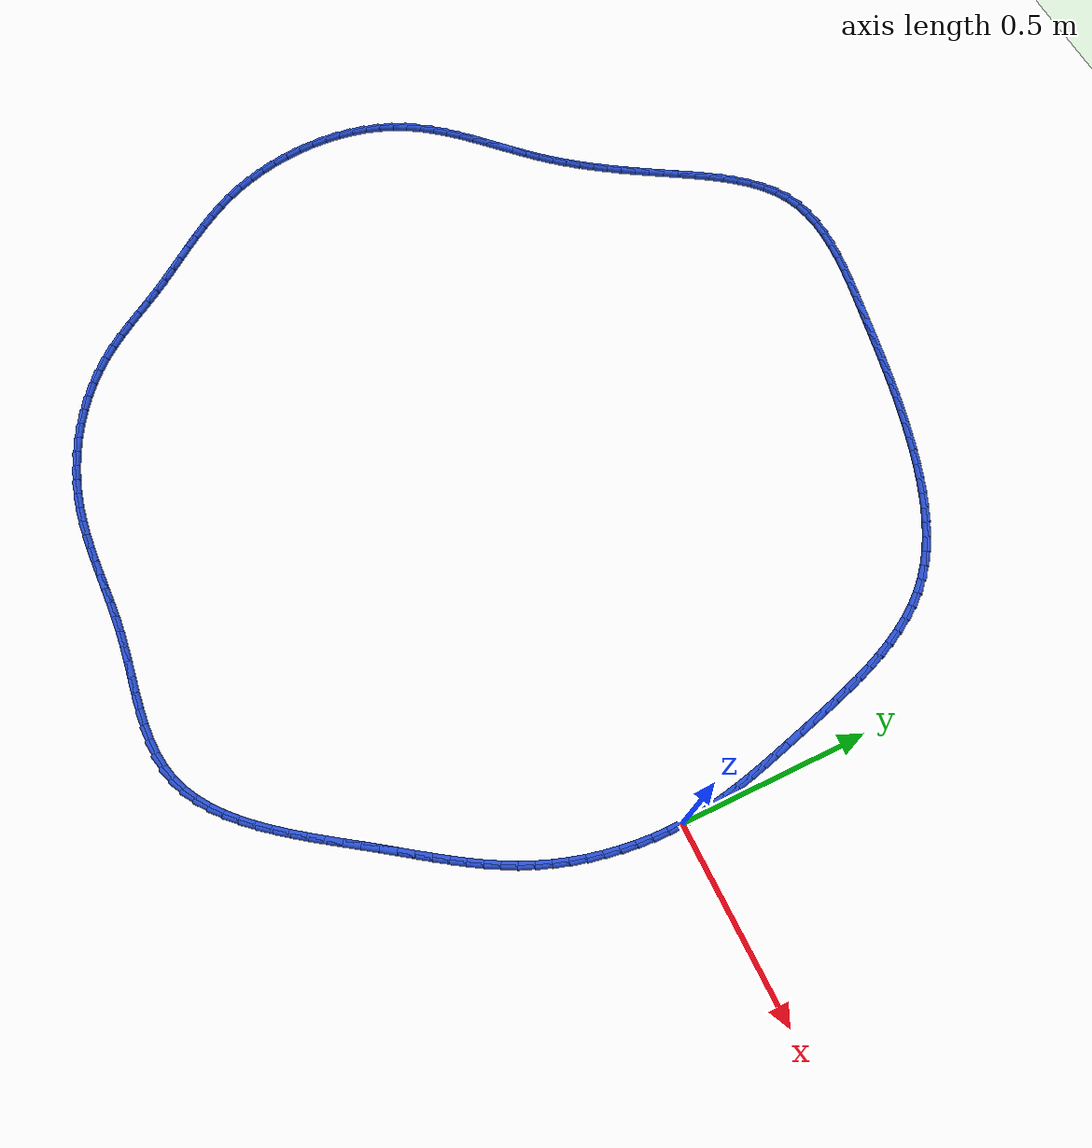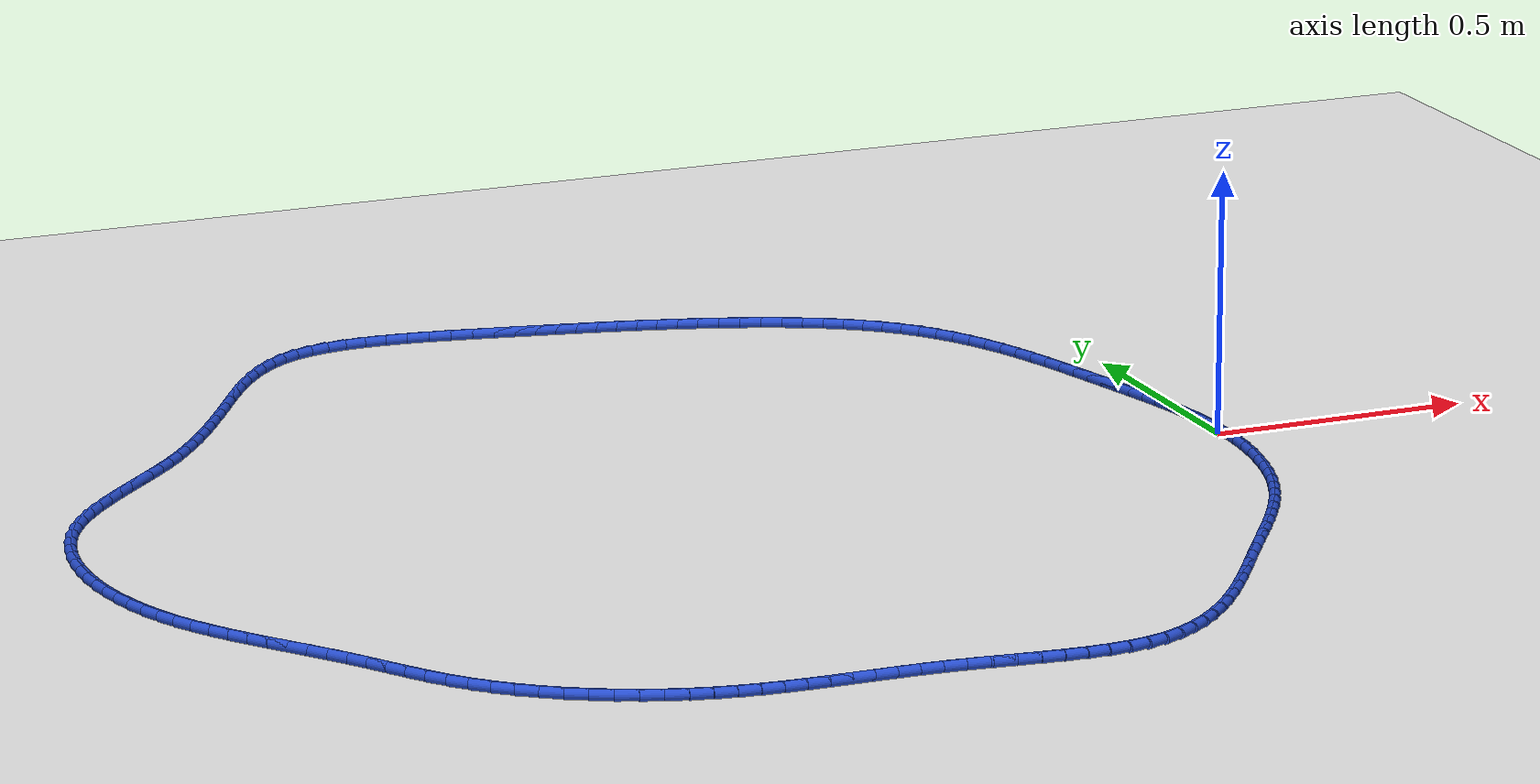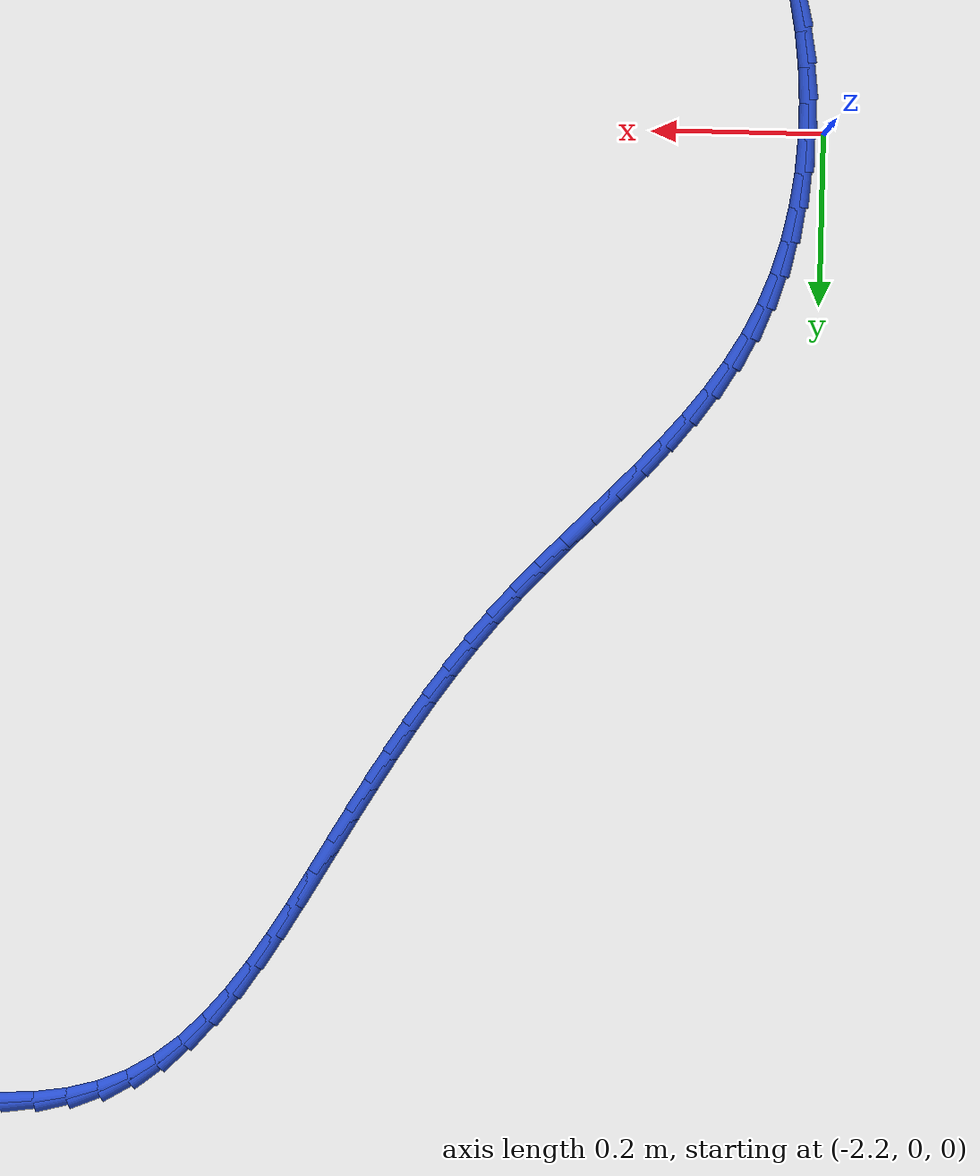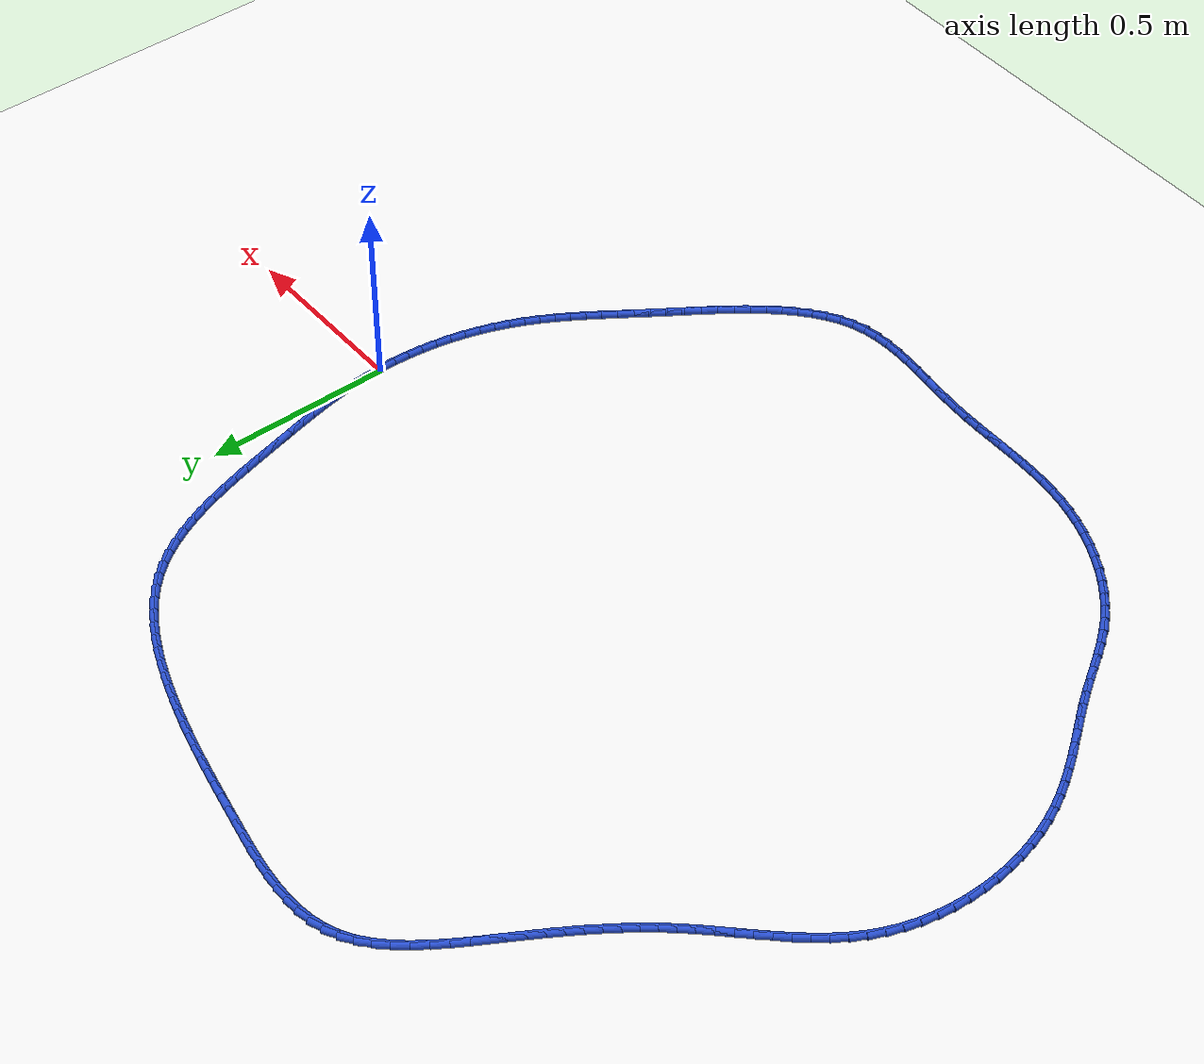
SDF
<sdf version="1.6">
 <world name="default">
  <light name="sun" type="directional">
   <pose>0 0 10 0 -0 0</pose>
   <diffuse>0.8 0.8 0.8 1</diffuse>
   <specular>0.2 0.2 0.2 1</specular>
   <attenuation>
    <range>1000</range>
    <constant>0.9</constant>
    <linear>0.01</linear>
    <quadratic>0.001</quadratic>
   </attenuation>
   <direction>-0.5 0.1 -0.9</direction>
  </light>
  <model name="ground_plane">
   <static>1</static>
   <link name="link">
    <collision name="collision">
     <geometry><plane><normal>0 0 1</normal><size>100 100</size></plane></geometry>
     <surface><friction><ode><mu>100</mu><mu2>50</mu2></ode></friction></surface>
    </collision>
    <visual name="visual">
     <cast_shadows>0</cast_shadows>
     <geometry><plane><normal>0 0 1</normal><size>100 100</size></plane></geometry>
     <material>
      <script><uri>file://media/materials/scripts/gazebo.material</uri><name>Gazebo/WhiteGlow</name></script>
     </material>
    </visual>
   </link>
  </model>
  <gravity>0 0 -9.8</gravity>
  <magnetic_field>6e-06 2.3e-05 -4.2e-05</magnetic_field>
  <atmosphere type="adiabatic"/>
  <physics name="default_physics" default="0" type="ode">
   <max_step_size>0.001</max_step_size>
   <real_time_factor>1</real_time_factor>
   <real_time_update_rate>1000</real_time_update_rate>
  </physics>
  <scene><ambient>0.4 0.4 0.4 1</ambient><background>0.7 0.7 0.7 1</background><shadows>1</shadows></scene>
  <spherical_coordinates>
   <surface_model>EARTH_WGS84</surface_model>
   <latitude_deg>0</latitude_deg>
   <longitude_deg>0</longitude_deg>
   <elevation>0</elevation>
   <heading_deg>0</heading_deg>
  </spherical_coordinates>
  <model name="line">
   <link name="link_0">
    <pose>-1.3877787807814457e-17 3.469446951953614e-17 0.01 0 1.57 -1.5139552277682178</pose>
    <collision name="collision">
     <geometry><cylinder><radius>0.01</radius><length>0.08</length></cylinder></geometry>
    </collision>
    <visual name="visual">
     <material>
      <script><name>Gazebo/Blue</name><uri>file://media/materials/scripts/gazebo.material</uri></script>
     </material>
     <geometry><cylinder><radius>0.01</radius><length>0.08</length></cylinder></geometry>
    </visual>
   </link>
   <link name="link_1">
    <pose>-0.0022696599464734476 0.03988689702617324 0.01 0 1.57 -1.4692420824111356</pose>
    <collision name="collision">
     <geometry><cylinder><radius>0.01</radius><length>0.08</length></cylinder></geometry>
    </collision>
    <visual name="visual">
     <material>
      <script><name>Gazebo/Blue</name><uri>file://media/materials/scripts/gazebo.material</uri></script>
     </material>
     <geometry><cylinder><radius>0.01</radius><length>0.08</length></cylinder></geometry>
    </visual>
   </link>
   <link name="link_2">
    <pose>-0.006303267038536477 0.07946900431053709 0.01 0 1.57 -1.4298986067800323</pose>
    <collision name="collision">
     <geometry><cylinder><radius>0.01</radius><length>0.08</length></cylinder></geometry>
    </collision>
    <visual name="visual">
     <material>
      <script><name>Gazebo/Blue</name><uri>file://media/materials/scripts/gazebo.material</uri></script>
     </material>
     <geometry><cylinder><radius>0.01</radius><length>0.08</length></cylinder></geometry>
    </visual>
   </link>
   <link name="link_3">
    <pose>-0.011885944081937164 0.1188286569059554 0.01 0 1.57 -1.3962285846299256</pose>
    <collision name="collision">
     <geometry><cylinder><radius>0.01</radius><length>0.08</length></cylinder></geometry>
    </collision>
    <visual name="visual">
     <material>
      <script><name>Gazebo/Blue</name><uri>file://media/materials/scripts/gazebo.material</uri></script>
     </material>
     <geometry><cylinder><radius>0.01</radius><length>0.08</length></cylinder></geometry>
    </visual>
   </link>
   <link name="link_4">
    <pose>-0.018802813882423556 0.15804818986529195 0.01 0 1.57 -1.3684010352273537</pose>
    <collision name="collision">
     <geometry><cylinder><radius>0.01</radius><length>0.08</length></cylinder></geometry>
    </collision>
    <visual name="visual">
     <material>
      <script><name>Gazebo/Blue</name><uri>file://media/materials/scripts/gazebo.material</uri></script>
     </material>
     <geometry><cylinder><radius>0.01</radius><length>0.08</length></cylinder></geometry>
    </visual>
   </link>
   <link name="link_5">
    <pose>-0.026838999245743733 0.19720993824141048 0.01 0 1.57 -1.3464791585278855</pose>
    <collision name="collision">
     <geometry><cylinder><radius>0.01</radius><length>0.08</length></cylinder></geometry>
    </collision>
    <visual name="visual">
     <material>
      <script><name>Gazebo/Blue</name><uri>file://media/materials/scripts/gazebo.material</uri></script>
     </material>
     <geometry><cylinder><radius>0.01</radius><length>0.08</length></cylinder></geometry>
    </visual>
   </link>
   <link name="link_6">
    <pose>-0.03577962297764574 0.23639623708717492 0.01 0 1.57 -1.3304485131201151</pose>
    <collision name="collision">
     <geometry><cylinder><radius>0.01</radius><length>0.08</length></cylinder></geometry>
    </collision>
    <visual name="visual">
     <material>
      <script><name>Gazebo/Blue</name><uri>file://media/materials/scripts/gazebo.material</uri></script>
     </material>
     <geometry><cylinder><radius>0.01</radius><length>0.08</length></cylinder></geometry>
    </visual>
   </link>
   <link name="link_7">
    <pose>-0.045409807883877634 0.2756894214554489 0.01 0 1.57 -1.3202410651064833</pose>
    <collision name="collision">
     <geometry><cylinder><radius>0.01</radius><length>0.08</length></cylinder></geometry>
    </collision>
    <visual name="visual">
     <material>
      <script><name>Gazebo/Blue</name><uri>file://media/materials/scripts/gazebo.material</uri></script>
     </material>
     <geometry><cylinder><radius>0.01</radius><length>0.08</length></cylinder></geometry>
    </visual>
   </link>
   <link name="link_8">
    <pose>-0.055514676770187524 0.3151718263990964 0.01 0 1.57 -1.3157534332609713</pose>
    <collision name="collision">
     <geometry><cylinder><radius>0.01</radius><length>0.08</length></cylinder></geometry>
    </collision>
    <visual name="visual">
     <material>
      <script><name>Gazebo/Blue</name><uri>file://media/materials/scripts/gazebo.material</uri></script>
     </material>
     <geometry><cylinder><radius>0.01</radius><length>0.08</length></cylinder></geometry>
    </visual>
   </link>
   <link name="link_9">
    <pose>-0.06587935244232342 0.35492578697098104 0.01 0 1.57 -1.3157178530848217</pose>
    <collision name="collision">
     <geometry><cylinder><radius>0.01</radius><length>0.08</length></cylinder></geometry>
    </collision>
    <visual name="visual">
     <material>
      <script><name>Gazebo/Blue</name><uri>file://media/materials/scripts/gazebo.material</uri></script>
     </material>
     <geometry><cylinder><radius>0.01</radius><length>0.08</length></cylinder></geometry>
    </visual>
   </link>
   <link name="link_10">
    <pose>-0.07633042953991581 0.3950053008226362 0.01 0 1.57 -1.3126921690269069</pose>
    <collision name="collision">
     <geometry><cylinder><radius>0.01</radius><length>0.08</length></cylinder></geometry>
    </collision>
    <visual name="visual">
     <material>
      <script><name>Gazebo/Blue</name><uri>file://media/materials/scripts/gazebo.material</uri></script>
     </material>
     <geometry><cylinder><radius>0.01</radius><length>0.08</length></cylinder></geometry>
    </visual>
   </link>
   <link name="link_11">
    <pose>-0.08696290580641364 0.4352809677242067 0.01 0 1.57 -1.303777895708684</pose>
    <collision name="collision">
     <geometry><cylinder><radius>0.01</radius><length>0.08</length></cylinder></geometry>
    </collision>
    <visual name="visual">
     <material>
      <script><name>Gazebo/Blue</name><uri>file://media/materials/scripts/gazebo.material</uri></script>
     </material>
     <geometry><cylinder><radius>0.01</radius><length>0.08</length></cylinder></geometry>
    </visual>
   </link>
   <link name="link_12">
    <pose>-0.09797863517364529 0.4755503733924119 0.01 0 1.57 -1.2889176322460891</pose>
    <collision name="collision">
     <geometry><cylinder><radius>0.01</radius><length>0.08</length></cylinder></geometry>
    </collision>
    <visual name="visual">
     <material>
      <script><name>Gazebo/Blue</name><uri>file://media/materials/scripts/gazebo.material</uri></script>
     </material>
     <geometry><cylinder><radius>0.01</radius><length>0.08</length></cylinder></geometry>
    </visual>
   </link>
   <link name="link_13">
    <pose>-0.10957974629239936 0.5156109158305108 0.01 0 1.57 -1.2679508675858402</pose>
    <collision name="collision">
     <geometry><cylinder><radius>0.01</radius><length>0.08</length></cylinder></geometry>
    </collision>
    <visual name="visual">
     <material>
      <script><name>Gazebo/Blue</name><uri>file://media/materials/scripts/gazebo.material</uri></script>
     </material>
     <geometry><cylinder><radius>0.01</radius><length>0.08</length></cylinder></geometry>
    </visual>
   </link>
   <link name="link_14">
    <pose>-0.12196836781346451 0.5552599930417621 0.01 0 1.57 -1.240617523162065</pose>
    <collision name="collision">
     <geometry><cylinder><radius>0.01</radius><length>0.08</length></cylinder></geometry>
    </collision>
    <visual name="visual">
     <material>
      <script><name>Gazebo/Blue</name><uri>file://media/materials/scripts/gazebo.material</uri></script>
     </material>
     <geometry><cylinder><radius>0.01</radius><length>0.08</length></cylinder></geometry>
    </visual>
   </link>
   <link name="link_15">
    <pose>-0.13534662838762937 0.5942950030294252 0.01 0 1.57 -1.2065738095816627</pose>
    <collision name="collision">
     <geometry><cylinder><radius>0.01</radius><length>0.08</length></cylinder></geometry>
    </collision>
    <visual name="visual">
     <material>
      <script><name>Gazebo/Blue</name><uri>file://media/materials/scripts/gazebo.material</uri></script>
     </material>
     <geometry><cylinder><radius>0.01</radius><length>0.08</length></cylinder></geometry>
    </visual>
   </link>
   <link name="link_16">
    <pose>-0.1499166566656826 0.6325133437967586 0.01 0 1.57 -1.1654171225708025</pose>
    <collision name="collision">
     <geometry><cylinder><radius>0.01</radius><length>0.08</length></cylinder></geometry>
    </collision>
    <visual name="visual">
     <material>
      <script><name>Gazebo/Blue</name><uri>file://media/materials/scripts/gazebo.material</uri></script>
     </material>
     <geometry><cylinder><radius>0.01</radius><length>0.08</length></cylinder></geometry>
    </visual>
   </link>
   <link name="link_17">
    <pose>-0.1658805812984129 0.669712413347022 0.01 0 1.57 -1.116725628355385</pose>
    <collision name="collision">
     <geometry><cylinder><radius>0.01</radius><length>0.08</length></cylinder></geometry>
    </collision>
    <visual name="visual">
     <material>
      <script><name>Gazebo/Blue</name><uri>file://media/materials/scripts/gazebo.material</uri></script>
     </material>
     <geometry><cylinder><radius>0.01</radius><length>0.08</length></cylinder></geometry>
    </visual>
   </link>
   <link name="link_18">
    <pose>-0.18344053093660878 0.7056896096834737 0.01 0 1.57 -1.0601190018402498</pose>
    <collision name="collision">
     <geometry><cylinder><radius>0.01</radius><length>0.08</length></cylinder></geometry>
    </collision>
    <visual name="visual">
     <material>
      <script><name>Gazebo/Blue</name><uri>file://media/materials/scripts/gazebo.material</uri></script>
     </material>
     <geometry><cylinder><radius>0.01</radius><length>0.08</length></cylinder></geometry>
    </visual>
   </link>
   <link name="link_19">
    <pose>-0.20279863423105893 0.7402423308093731 0.01 0 1.57 -0.9953457853929073</pose>
    <collision name="collision">
     <geometry><cylinder><radius>0.01</radius><length>0.08</length></cylinder></geometry>
    </collision>
    <visual name="visual">
     <material>
      <script><name>Gazebo/Blue</name><uri>file://media/materials/scripts/gazebo.material</uri></script>
     </material>
     <geometry><cylinder><radius>0.01</radius><length>0.08</length></cylinder></geometry>
    </visual>
   </link>
   <link name="link_20">
    <pose>-0.22415701983255204 0.773167974727979 0.01 0 1.57 -0.9223979871179626</pose>
    <collision name="collision">
     <geometry><cylinder><radius>0.01</radius><length>0.08</length></cylinder></geometry>
    </collision>
    <visual name="visual">
     <material>
      <script><name>Gazebo/Blue</name><uri>file://media/materials/scripts/gazebo.material</uri></script>
     </material>
     <geometry><cylinder><radius>0.01</radius><length>0.08</length></cylinder></geometry>
    </visual>
   </link>
   <link name="link_21">
    <pose>-0.24771781639187673 0.8042639394425507 0.01 0 1.57 -0.8416430142504149</pose>
    <collision name="collision">
     <geometry><cylinder><radius>0.01</radius><length>0.08</length></cylinder></geometry>
    </collision>
    <visual name="visual">
     <material>
      <script><name>Gazebo/Blue</name><uri>file://media/materials/scripts/gazebo.material</uri></script>
     </material>
     <geometry><cylinder><radius>0.01</radius><length>0.08</length></cylinder></geometry>
    </visual>
   </link>
   <link name="link_22">
    <pose>-0.273683140991958 0.8333276307336495 0.01 0 1.57 -0.7567832264424561</pose>
    <collision name="collision">
     <geometry><cylinder><radius>0.01</radius><length>0.08</length></cylinder></geometry>
    </collision>
    <visual name="visual">
     <material>
      <script><name>Gazebo/Blue</name><uri>file://media/materials/scripts/gazebo.material</uri></script>
     </material>
     <geometry><cylinder><radius>0.01</radius><length>0.08</length></cylinder></geometry>
    </visual>
   </link>
   <link name="link_23">
    <pose>-0.3021604452552976 0.860220099837204 0.01 0 1.57 -0.6783331806806251</pose>
    <collision name="collision">
     <geometry><cylinder><radius>0.01</radius><length>0.08</length></cylinder></geometry>
    </collision>
    <visual name="visual">
     <material>
      <script><name>Gazebo/Blue</name><uri>file://media/materials/scripts/gazebo.material</uri></script>
     </material>
     <geometry><cylinder><radius>0.01</radius><length>0.08</length></cylinder></geometry>
    </visual>
   </link>
   <link name="link_24">
    <pose>-0.3329332670541112 0.8850201715893977 0.01 0 1.57 -0.6083714480800783</pose>
    <collision name="collision">
     <geometry><cylinder><radius>0.01</radius><length>0.08</length></cylinder></geometry>
    </collision>
    <visual name="visual">
     <material>
      <script><name>Gazebo/Blue</name><uri>file://media/materials/scripts/gazebo.material</uri></script>
     </material>
     <geometry><cylinder><radius>0.01</radius><length>0.08</length></cylinder></geometry>
    </visual>
   </link>
   <link name="link_25">
    <pose>-0.36571592222374666 0.9078532101665094 0.01 0 1.57 -0.5465187247359409</pose>
    <collision name="collision">
     <geometry><cylinder><radius>0.01</radius><length>0.08</length></cylinder></geometry>
    </collision>
    <visual name="visual">
     <material>
      <script><name>Gazebo/Blue</name><uri>file://media/materials/scripts/gazebo.material</uri></script>
     </material>
     <geometry><cylinder><radius>0.01</radius><length>0.08</length></cylinder></geometry>
    </visual>
   </link>
   <link name="link_26">
    <pose>-0.40022272659955194 0.9288445797448175 0.01 0 1.57 -0.4922126759041056</pose>
    <collision name="collision">
     <geometry><cylinder><radius>0.01</radius><length>0.08</length></cylinder></geometry>
    </collision>
    <visual name="visual">
     <material>
      <script><name>Gazebo/Blue</name><uri>file://media/materials/scripts/gazebo.material</uri></script>
     </material>
     <geometry><cylinder><radius>0.01</radius><length>0.08</length></cylinder></geometry>
    </visual>
   </link>
   <link name="link_27">
    <pose>-0.4361679960168748 0.9481196445006006 0.01 0 1.57 -0.4448231258099982</pose>
    <collision name="collision">
     <geometry><cylinder><radius>0.01</radius><length>0.08</length></cylinder></geometry>
    </collision>
    <visual name="visual">
     <material>
      <script><name>Gazebo/Blue</name><uri>file://media/materials/scripts/gazebo.material</uri></script>
     </material>
     <geometry><cylinder><radius>0.01</radius><length>0.08</length></cylinder></geometry>
    </visual>
   </link>
   <link name="link_28">
    <pose>-0.4732660463110633 0.9658037686101374 0.01 0 1.57 -0.4037289561167457</pose>
    <collision name="collision">
     <geometry><cylinder><radius>0.01</radius><length>0.08</length></cylinder></geometry>
    </collision>
    <visual name="visual">
     <material>
      <script><name>Gazebo/Blue</name><uri>file://media/materials/scripts/gazebo.material</uri></script>
     </material>
     <geometry><cylinder><radius>0.01</radius><length>0.08</length></cylinder></geometry>
    </visual>
   </link>
   <link name="link_29">
    <pose>-0.5112311933174651 0.982022316249706 0.01 0 1.57 -0.36836508496423526</pose>
    <collision name="collision">
     <geometry><cylinder><radius>0.01</radius><length>0.08</length></cylinder></geometry>
    </collision>
    <visual name="visual">
     <material>
      <script><name>Gazebo/Blue</name><uri>file://media/materials/scripts/gazebo.material</uri></script>
     </material>
     <geometry><cylinder><radius>0.01</radius><length>0.08</length></cylinder></geometry>
    </visual>
   </link>
   <link name="link_30">
    <pose>-0.549777752871428 0.9969006515955852 0.01 0 1.57 -0.33824931033730843</pose>
    <collision name="collision">
     <geometry><cylinder><radius>0.01</radius><length>0.08</length></cylinder></geometry>
    </collision>
    <visual name="visual">
     <material>
      <script><name>Gazebo/Blue</name><uri>file://media/materials/scripts/gazebo.material</uri></script>
     </material>
     <geometry><cylinder><radius>0.01</radius><length>0.08</length></cylinder></geometry>
    </visual>
   </link>
   <link name="link_31">
    <pose>-0.5886200408083001 1.0105641388240534 0.01 0 1.57 -0.3129974786201981</pose>
    <collision name="collision">
     <geometry><cylinder><radius>0.01</radius><length>0.08</length></cylinder></geometry>
    </collision>
    <visual name="visual">
     <material>
      <script><name>Gazebo/Blue</name><uri>file://media/materials/scripts/gazebo.material</uri></script>
     </material>
     <geometry><cylinder><radius>0.01</radius><length>0.08</length></cylinder></geometry>
    </visual>
   </link>
   <link name="link_32">
    <pose>-0.6274723729634293 1.0231381421113892 0.01 0 1.57 -0.29203549179892146</pose>
    <collision name="collision">
     <geometry><cylinder><radius>0.01</radius><length>0.08</length></cylinder></geometry>
    </collision>
    <visual name="visual">
     <material>
      <script><name>Gazebo/Blue</name><uri>file://media/materials/scripts/gazebo.material</uri></script>
     </material>
     <geometry><cylinder><radius>0.01</radius><length>0.08</length></cylinder></geometry>
    </visual>
   </link>
   <link name="link_33">
    <pose>-0.6660878102384947 1.0347471353747213 0.01 0 1.57 -0.2733091390741443</pose>
    <collision name="collision">
     <geometry><cylinder><radius>0.01</radius><length>0.08</length></cylinder></geometry>
    </collision>
    <visual name="visual">
     <material>
      <script><name>Gazebo/Blue</name><uri>file://media/materials/scripts/gazebo.material</uri></script>
     </material>
     <geometry><cylinder><radius>0.01</radius><length>0.08</length></cylinder></geometry>
    </visual>
   </link>
   <link name="link_34">
    <pose>-0.7044807144597042 1.0455095885270316 0.01 0 1.57 -0.25622118988302034</pose>
    <collision name="collision">
     <geometry><cylinder><radius>0.01</radius><length>0.08</length></cylinder></geometry>
    </collision>
    <visual name="visual">
     <material>
      <script><name>Gazebo/Blue</name><uri>file://media/materials/scripts/gazebo.material</uri></script>
     </material>
     <geometry><cylinder><radius>0.01</radius><length>0.08</length></cylinder></geometry>
    </visual>
   </link>
   <link name="link_35">
    <pose>-0.7427734325652713 1.0555414902690323 0.01 0 1.57 -0.24100829451175523</pose>
    <collision name="collision">
     <geometry><cylinder><radius>0.01</radius><length>0.08</length></cylinder></geometry>
    </collision>
    <visual name="visual">
     <material>
      <script><name>Gazebo/Blue</name><uri>file://media/materials/scripts/gazebo.material</uri></script>
     </material>
     <geometry><cylinder><radius>0.01</radius><length>0.08</length></cylinder></geometry>
    </visual>
   </link>
   <link name="link_36">
    <pose>-0.7810886531599219 1.064958821450841 0.01 0 1.57 -0.22786655160856303</pose>
    <collision name="collision">
     <geometry><cylinder><radius>0.01</radius><length>0.08</length></cylinder></geometry>
    </collision>
    <visual name="visual">
     <material>
      <script><name>Gazebo/Blue</name><uri>file://media/materials/scripts/gazebo.material</uri></script>
     </material>
     <geometry><cylinder><radius>0.01</radius><length>0.08</length></cylinder></geometry>
    </visual>
   </link>
   <link name="link_37">
    <pose>-0.8195490648483821 1.0738775629225774 0.01 0 1.57 -0.2169420798759481</pose>
    <collision name="collision">
     <geometry><cylinder><radius>0.01</radius><length>0.08</length></cylinder></geometry>
    </collision>
    <visual name="visual">
     <material>
      <script><name>Gazebo/Blue</name><uri>file://media/materials/scripts/gazebo.material</uri></script>
     </material>
     <geometry><cylinder><radius>0.01</radius><length>0.08</length></cylinder></geometry>
    </visual>
   </link>
   <link name="link_38">
    <pose>-0.8582773562353774 1.08241369553436 0.01 0 1.57 -0.2083272432043862</pose>
    <collision name="collision">
     <geometry><cylinder><radius>0.01</radius><length>0.08</length></cylinder></geometry>
    </collision>
    <visual name="visual">
     <material>
      <script><name>Gazebo/Blue</name><uri>file://media/materials/scripts/gazebo.material</uri></script>
     </material>
     <geometry><cylinder><radius>0.01</radius><length>0.08</length></cylinder></geometry>
    </visual>
   </link>
   <link name="link_39">
    <pose>-0.8973962159256348 1.090683200136308 0.01 0 1.57 -0.20205992985741272</pose>
    <collision name="collision">
     <geometry><cylinder><radius>0.01</radius><length>0.08</length></cylinder></geometry>
    </collision>
    <visual name="visual">
     <material>
      <script><name>Gazebo/Blue</name><uri>file://media/materials/scripts/gazebo.material</uri></script>
     </material>
     <geometry><cylinder><radius>0.01</radius><length>0.08</length></cylinder></geometry>
    </visual>
   </link>
   <link name="link_40">
    <pose>-0.937028332523879 1.098802057578539 0.01 0 1.57 -0.1981256249751022</pose>
    <collision name="collision">
     <geometry><cylinder><radius>0.01</radius><length>0.08</length></cylinder></geometry>
    </collision>
    <visual name="visual">
     <material>
      <script><name>Gazebo/Blue</name><uri>file://media/materials/scripts/gazebo.material</uri></script>
     </material>
     <geometry><cylinder><radius>0.01</radius><length>0.08</length></cylinder></geometry>
    </visual>
   </link>
   <link name="link_41">
    <pose>-0.977296394634837 1.1068862487111732 0.01 0 1.57 -0.19646051709394793</pose>
    <collision name="collision">
     <geometry><cylinder><radius>0.01</radius><length>0.08</length></cylinder></geometry>
    </collision>
    <visual name="visual">
     <material>
      <script><name>Gazebo/Blue</name><uri>file://media/materials/scripts/gazebo.material</uri></script>
     </material>
     <geometry><cylinder><radius>0.01</radius><length>0.08</length></cylinder></geometry>
    </visual>
   </link>
   <link name="link_42">
    <pose>-1.0183230453723155 1.1150516901670953 0.01 0 1.57 -0.19428167143168013</pose>
    <collision name="collision">
     <geometry><cylinder><radius>0.01</radius><length>0.08</length></cylinder></geometry>
    </collision>
    <visual name="visual">
     <material>
      <script><name>Gazebo/Blue</name><uri>file://media/materials/scripts/gazebo.material</uri></script>
     </material>
     <geometry><cylinder><radius>0.01</radius><length>0.08</length></cylinder></geometry>
    </visual>
   </link>
   <link name="link_43">
    <pose>-1.0601348989069823 1.1232787393675463 0.01 0 1.57 -0.18332741471772562</pose>
    <collision name="collision">
     <geometry><cylinder><radius>0.01</radius><length>0.08</length></cylinder></geometry>
    </collision>
    <visual name="visual">
     <material>
      <script><name>Gazebo/Blue</name><uri>file://media/materials/scripts/gazebo.material</uri></script>
     </material>
     <geometry><cylinder><radius>0.01</radius><length>0.08</length></cylinder></geometry>
    </visual>
   </link>
   <link name="link_44">
    <pose>-1.1024599388031093 1.1311261919811093 0.01 0 1.57 -0.16194758488630512</pose>
    <collision name="collision">
     <geometry><cylinder><radius>0.01</radius><length>0.08</length></cylinder></geometry>
    </collision>
    <visual name="visual">
     <material>
      <script><name>Gazebo/Blue</name><uri>file://media/materials/scripts/gazebo.material</uri></script>
     </material>
     <geometry><cylinder><radius>0.01</radius><length>0.08</length></cylinder></geometry>
    </visual>
   </link>
   <link name="link_45">
    <pose>-1.1449682665481016 1.138071134470249 0.01 0 1.57 -0.12956506492319844</pose>
    <collision name="collision">
     <geometry><cylinder><radius>0.01</radius><length>0.08</length></cylinder></geometry>
    </collision>
    <visual name="visual">
     <material>
      <script><name>Gazebo/Blue</name><uri>file://media/materials/scripts/gazebo.material</uri></script>
     </material>
     <geometry><cylinder><radius>0.01</radius><length>0.08</length></cylinder></geometry>
    </visual>
   </link>
   <link name="link_46">
    <pose>-1.1873299836293625 1.1435906532974287 0.01 0 1.57 -0.08505546054984053</pose>
    <collision name="collision">
     <geometry><cylinder><radius>0.01</radius><length>0.08</length></cylinder></geometry>
    </collision>
    <visual name="visual">
     <material>
      <script><name>Gazebo/Blue</name><uri>file://media/materials/scripts/gazebo.material</uri></script>
     </material>
     <geometry><cylinder><radius>0.01</radius><length>0.08</length></cylinder></geometry>
    </visual>
   </link>
   <link name="link_47">
    <pose>-1.2292151915342975 1.147161834925113 0.01 0 1.57 -0.02676972377118209</pose>
    <collision name="collision">
     <geometry><cylinder><radius>0.01</radius><length>0.08</length></cylinder></geometry>
    </collision>
    <visual name="visual">
     <material>
      <script><name>Gazebo/Blue</name><uri>file://media/materials/scripts/gazebo.material</uri></script>
     </material>
     <geometry><cylinder><radius>0.01</radius><length>0.08</length></cylinder></geometry>
    </visual>
   </link>
   <link name="link_48">
    <pose>-1.2702939917503113 1.1482617658157661 0.01 0 1.57 0.04738850882438777</pose>
    <collision name="collision">
     <geometry><cylinder><radius>0.01</radius><length>0.08</length></cylinder></geometry>
    </collision>
    <visual name="visual">
     <material>
      <script><name>Gazebo/Blue</name><uri>file://media/materials/scripts/gazebo.material</uri></script>
     </material>
     <geometry><cylinder><radius>0.01</radius><length>0.08</length></cylinder></geometry>
    </visual>
   </link>
   <link name="link_49">
    <pose>-1.310236485764808 1.1463675324318516 0.01 0 1.57 0.13972373295222726</pose>
    <collision name="collision">
     <geometry><cylinder><radius>0.01</radius><length>0.08</length></cylinder></geometry>
    </collision>
    <visual name="visual">
     <material>
      <script><name>Gazebo/Blue</name><uri>file://media/materials/scripts/gazebo.material</uri></script>
     </material>
     <geometry><cylinder><radius>0.01</radius><length>0.08</length></cylinder></geometry>
    </visual>
   </link>
   <link name="link_50">
    <pose>-1.3487127750651937 1.1409562212358342 0.01 0 1.57 0.2521822867691816</pose>
    <collision name="collision">
     <geometry><cylinder><radius>0.01</radius><length>0.08</length></cylinder></geometry>
    </collision>
    <visual name="visual">
     <material>
      <script><name>Gazebo/Blue</name><uri>file://media/materials/scripts/gazebo.material</uri></script>
     </material>
     <geometry><cylinder><radius>0.01</radius><length>0.08</length></cylinder></geometry>
    </visual>
   </link>
   <link name="link_51">
    <pose>-1.3853929611388722 1.1315049186901782 0.01 0 1.57 0.3853005220369759</pose>
    <collision name="collision">
     <geometry><cylinder><radius>0.01</radius><length>0.08</length></cylinder></geometry>
    </collision>
    <visual name="visual">
     <material>
      <script><name>Gazebo/Blue</name><uri>file://media/materials/scripts/gazebo.material</uri></script>
     </material>
     <geometry><cylinder><radius>0.01</radius><length>0.08</length></cylinder></geometry>
    </visual>
   </link>
   <link name="link_52">
    <pose>-1.419947145473248 1.1174907112573467 0.01 0 1.57 0.5320045049402204</pose>
    <collision name="collision">
     <geometry><cylinder><radius>0.01</radius><length>0.08</length></cylinder></geometry>
    </collision>
    <visual name="visual">
     <material>
      <script><name>Gazebo/Blue</name><uri>file://media/materials/scripts/gazebo.material</uri></script>
     </material>
     <geometry><cylinder><radius>0.01</radius><length>0.08</length></cylinder></geometry>
    </visual>
   </link>
   <link name="link_53">
    <pose>-1.4521247197903533 1.09855057813262 0.01 0 1.57 0.6644192034709292</pose>
    <collision name="collision">
     <geometry><cylinder><radius>0.01</radius><length>0.08</length></cylinder></geometry>
    </collision>
    <visual name="visual">
     <material>
      <script><name>Gazebo/Blue</name><uri>file://media/materials/scripts/gazebo.material</uri></script>
     </material>
     <geometry><cylinder><radius>0.01</radius><length>0.08</length></cylinder></geometry>
    </visual>
   </link>
   <link name="link_54">
    <pose>-1.4820625852912466 1.0751029308009559 0.01 0 1.57 0.773546375072764</pose>
    <collision name="collision">
     <geometry><cylinder><radius>0.01</radius><length>0.08</length></cylinder></geometry>
    </collision>
    <visual name="visual">
     <material>
      <script><name>Gazebo/Blue</name><uri>file://media/materials/scripts/gazebo.material</uri></script>
     </material>
     <geometry><cylinder><radius>0.01</radius><length>0.08</length></cylinder></geometry>
    </visual>
   </link>
   <link name="link_55">
    <pose>-1.5100158423467054 1.047804535298178 0.01 0 1.57 0.8605180991703288</pose>
    <collision name="collision">
     <geometry><cylinder><radius>0.01</radius><length>0.08</length></cylinder></geometry>
    </collision>
    <visual name="visual">
     <material>
      <script><name>Gazebo/Blue</name><uri>file://media/materials/scripts/gazebo.material</uri></script>
     </material>
     <geometry><cylinder><radius>0.01</radius><length>0.08</length></cylinder></geometry>
    </visual>
   </link>
   <link name="link_56">
    <pose>-1.5362396201394153 1.0173122157607735 0.01 0 1.57 0.9277339892497062</pose>
    <collision name="collision">
     <geometry><cylinder><radius>0.01</radius><length>0.08</length></cylinder></geometry>
    </collision>
    <visual name="visual">
     <material>
      <script><name>Gazebo/Blue</name><uri>file://media/materials/scripts/gazebo.material</uri></script>
     </material>
     <geometry><cylinder><radius>0.01</radius><length>0.08</length></cylinder></geometry>
    </visual>
   </link>
   <link name="link_57">
    <pose>-1.5609890478520656 0.9842827963252296 0.01 0 1.57 0.9777128486224795</pose>
    <collision name="collision">
     <geometry><cylinder><radius>0.01</radius><length>0.08</length></cylinder></geometry>
    </collision>
    <visual name="visual">
     <material>
      <script><name>Gazebo/Blue</name><uri>file://media/materials/scripts/gazebo.material</uri></script>
     </material>
     <geometry><cylinder><radius>0.01</radius><length>0.08</length></cylinder></geometry>
    </visual>
   </link>
   <link name="link_58">
    <pose>-1.5845192546673426 0.9493731011280323 0.01 0 1.57 1.012537431328297</pose>
    <collision name="collision">
     <geometry><cylinder><radius>0.01</radius><length>0.08</length></cylinder></geometry>
    </collision>
    <visual name="visual">
     <material>
      <script><name>Gazebo/Blue</name><uri>file://media/materials/scripts/gazebo.material</uri></script>
     </material>
     <geometry><cylinder><radius>0.01</radius><length>0.08</length></cylinder></geometry>
    </visual>
   </link>
   <link name="link_59">
    <pose>-1.607085369767934 0.9132399543056702 0.01 0 1.57 1.033643201926098</pose>
    <collision name="collision">
     <geometry><cylinder><radius>0.01</radius><length>0.08</length></cylinder></geometry>
    </collision>
    <visual name="visual">
     <material>
      <script><name>Gazebo/Blue</name><uri>file://media/materials/scripts/gazebo.material</uri></script>
     </material>
     <geometry><cylinder><radius>0.01</radius><length>0.08</length></cylinder></geometry>
    </visual>
   </link>
   <link name="link_60">
    <pose>-1.6289425223365264 0.8765401799946287 0.01 0 1.57 1.0417496330772755</pose>
    <collision name="collision">
     <geometry><cylinder><radius>0.01</radius><length>0.08</length></cylinder></geometry>
    </collision>
    <visual name="visual">
     <material>
      <script><name>Gazebo/Blue</name><uri>file://media/materials/scripts/gazebo.material</uri></script>
     </material>
     <geometry><cylinder><radius>0.01</radius><length>0.08</length></cylinder></geometry>
    </visual>
   </link>
   <link name="link_61">
    <pose>-1.6503458415558088 0.8399306023313952 0.01 0 1.57 1.0383585355463547</pose>
    <collision name="collision">
     <geometry><cylinder><radius>0.01</radius><length>0.08</length></cylinder></geometry>
    </collision>
    <visual name="visual">
     <material>
      <script><name>Gazebo/Blue</name><uri>file://media/materials/scripts/gazebo.material</uri></script>
     </material>
     <geometry><cylinder><radius>0.01</radius><length>0.08</length></cylinder></geometry>
    </visual>
   </link>
   <link name="link_62">
    <pose>-1.671538058365785 0.8039626002420689 0.01 0 1.57 1.0295249355186633</pose>
    <collision name="collision">
     <geometry><cylinder><radius>0.01</radius><length>0.08</length></cylinder></geometry>
    </collision>
    <visual name="visual">
     <material>
      <script><name>Gazebo/Blue</name><uri>file://media/materials/scripts/gazebo.material</uri></script>
     </material>
     <geometry><cylinder><radius>0.01</radius><length>0.08</length></cylinder></geometry>
    </visual>
   </link>
   <link name="link_63">
    <pose>-1.692709798552582 0.7687444060669937 0.01 0 1.57 1.0167913188544366</pose>
    <collision name="collision">
     <geometry><cylinder><radius>0.01</radius><length>0.08</length></cylinder></geometry>
    </collision>
    <visual name="visual">
     <material>
      <script><name>Gazebo/Blue</name><uri>file://media/materials/scripts/gazebo.material</uri></script>
     </material>
     <geometry><cylinder><radius>0.01</radius><length>0.08</length></cylinder></geometry>
    </visual>
   </link>
   <link name="link_64">
    <pose>-1.7140380020775752 0.7342678562421205 0.01 0 1.57 1.000095883421319</pose>
    <collision name="collision">
     <geometry><cylinder><radius>0.01</radius><length>0.08</length></cylinder></geometry>
    </collision>
    <visual name="visual">
     <material>
      <script><name>Gazebo/Blue</name><uri>file://media/materials/scripts/gazebo.material</uri></script>
     </material>
     <geometry><cylinder><radius>0.01</radius><length>0.08</length></cylinder></geometry>
    </visual>
   </link>
   <link name="link_65">
    <pose>-1.7356996088439323 0.7005247867083332 0.01 0 1.57 0.9794439962837515</pose>
    <collision name="collision">
     <geometry><cylinder><radius>0.01</radius><length>0.08</length></cylinder></geometry>
    </collision>
    <visual name="visual">
     <material>
      <script><name>Gazebo/Blue</name><uri>file://media/materials/scripts/gazebo.material</uri></script>
     </material>
     <geometry><cylinder><radius>0.01</radius><length>0.08</length></cylinder></geometry>
    </visual>
   </link>
   <link name="link_66">
    <pose>-1.7578715587548208 0.6675070334065157 0.01 0 1.57 0.9549192374638674</pose>
    <collision name="collision">
     <geometry><cylinder><radius>0.01</radius><length>0.08</length></cylinder></geometry>
    </collision>
    <visual name="visual">
     <material>
      <script><name>Gazebo/Blue</name><uri>file://media/materials/scripts/gazebo.material</uri></script>
     </material>
     <geometry><cylinder><radius>0.01</radius><length>0.08</length></cylinder></geometry>
    </visual>
   </link>
   <link name="link_67">
    <pose>-1.7807307917134088 0.6352064322775527 0.01 0 1.57 0.9266928767374412</pose>
    <collision name="collision">
     <geometry><cylinder><radius>0.01</radius><length>0.08</length></cylinder></geometry>
    </collision>
    <visual name="visual">
     <material>
      <script><name>Gazebo/Blue</name><uri>file://media/materials/scripts/gazebo.material</uri></script>
     </material>
     <geometry><cylinder><radius>0.01</radius><length>0.08</length></cylinder></geometry>
    </visual>
   </link>
   <link name="link_68">
    <pose>-1.8044542476228629 0.6036148192623279 0.01 0 1.57 0.8950300388147823</pose>
    <collision name="collision">
     <geometry><cylinder><radius>0.01</radius><length>0.08</length></cylinder></geometry>
    </collision>
    <visual name="visual">
     <material>
      <script><name>Gazebo/Blue</name><uri>file://media/materials/scripts/gazebo.material</uri></script>
     </material>
     <geometry><cylinder><radius>0.01</radius><length>0.08</length></cylinder></geometry>
    </visual>
   </link>
   <link name="link_69">
    <pose>-1.8292188663863507 0.5727240303017256 0.01 0 1.57 0.8602952147108077</pose>
    <collision name="collision">
     <geometry><cylinder><radius>0.01</radius><length>0.08</length></cylinder></geometry>
    </collision>
    <visual name="visual">
     <material>
      <script><name>Gazebo/Blue</name><uri>file://media/materials/scripts/gazebo.material</uri></script>
     </material>
     <geometry><cylinder><radius>0.01</radius><length>0.08</length></cylinder></geometry>
    </visual>
   </link>
   <link name="link_70">
    <pose>-1.8552014061850548 0.5425258333587705 0.01 0 1.57 0.826344097620378</pose>
    <collision name="collision">
     <geometry><cylinder><radius>0.01</radius><length>0.08</length></cylinder></geometry>
    </collision>
    <visual name="visual">
     <material>
      <script><name>Gazebo/Blue</name><uri>file://media/materials/scripts/gazebo.material</uri></script>
     </material>
     <geometry><cylinder><radius>0.01</radius><length>0.08</length></cylinder></geometry>
    </visual>
   </link>
   <link name="link_71">
    <pose>-1.8824399244155716 0.5129601117417195 0.01 0 1.57 0.8026957829965594</pose>
    <collision name="collision">
     <geometry><cylinder><radius>0.01</radius><length>0.08</length></cylinder></geometry>
    </collision>
    <visual name="visual">
     <material>
      <script><name>Gazebo/Blue</name><uri>file://media/materials/scripts/gazebo.material</uri></script>
     </material>
     <geometry><cylinder><radius>0.01</radius><length>0.08</length></cylinder></geometry>
    </visual>
   </link>
   <link name="link_72">
    <pose>-1.9105866382448273 0.48382241513324015 0.01 0 1.57 0.7905813712806803</pose>
    <collision name="collision">
     <geometry><cylinder><radius>0.01</radius><length>0.08</length></cylinder></geometry>
    </collision>
    <visual name="visual">
     <material>
      <script><name>Gazebo/Blue</name><uri>file://media/materials/scripts/gazebo.material</uri></script>
     </material>
     <geometry><cylinder><radius>0.01</radius><length>0.08</length></cylinder></geometry>
    </visual>
   </link>
   <link name="link_73">
    <pose>-1.9392272078807766 0.45488339584538223 0.01 0 1.57 0.7897247957297865</pose>
    <collision name="collision">
     <geometry><cylinder><radius>0.01</radius><length>0.08</length></cylinder></geometry>
    </collision>
    <visual name="visual">
     <material>
      <script><name>Gazebo/Blue</name><uri>file://media/materials/scripts/gazebo.material</uri></script>
     </material>
     <geometry><cylinder><radius>0.01</radius><length>0.08</length></cylinder></geometry>
    </visual>
   </link>
   <link name="link_74">
    <pose>-1.9679472935313709 0.42591370619019475 0.01 0 1.57 0.8000538229155463</pose>
    <collision name="collision">
     <geometry><cylinder><radius>0.01</radius><length>0.08</length></cylinder></geometry>
    </collision>
    <visual name="visual">
     <material>
      <script><name>Gazebo/Blue</name><uri>file://media/materials/scripts/gazebo.material</uri></script>
     </material>
     <geometry><cylinder><radius>0.01</radius><length>0.08</length></cylinder></geometry>
    </visual>
   </link>
   <link name="link_75">
    <pose>-1.9963325554045637 0.3966839984797282 0.01 0 1.57 0.8216993380148074</pose>
    <collision name="collision">
     <geometry><cylinder><radius>0.01</radius><length>0.08</length></cylinder></geometry>
    </collision>
    <visual name="visual">
     <material>
      <script><name>Gazebo/Blue</name><uri>file://media/materials/scripts/gazebo.material</uri></script>
     </material>
     <geometry><cylinder><radius>0.01</radius><length>0.08</length></cylinder></geometry>
    </visual>
   </link>
   <link name="link_76">
    <pose>-2.023968653708307 0.36696492502603195 0.01 0 1.57 0.8549600620321234</pose>
    <collision name="collision">
     <geometry><cylinder><radius>0.01</radius><length>0.08</length></cylinder></geometry>
    </collision>
    <visual name="visual">
     <material>
      <script><name>Gazebo/Blue</name><uri>file://media/materials/scripts/gazebo.material</uri></script>
     </material>
     <geometry><cylinder><radius>0.01</radius><length>0.08</length></cylinder></geometry>
    </visual>
   </link>
   <link name="link_77">
    <pose>-2.0504412486505554 0.33652713814115554 0.01 0 1.57 0.9002253357698284</pose>
    <collision name="collision">
     <geometry><cylinder><radius>0.01</radius><length>0.08</length></cylinder></geometry>
    </collision>
    <visual name="visual">
     <material>
      <script><name>Gazebo/Blue</name><uri>file://media/materials/scripts/gazebo.material</uri></script>
     </material>
     <geometry><cylinder><radius>0.01</radius><length>0.08</length></cylinder></geometry>
    </visual>
   </link>
   <link name="link_78">
    <pose>-2.07533600043926 0.305141290137149 0.01 0 1.57 0.9578419690824351</pose>
    <collision name="collision">
     <geometry><cylinder><radius>0.01</radius><length>0.08</length></cylinder></geometry>
    </collision>
    <visual name="visual">
     <material>
      <script><name>Gazebo/Blue</name><uri>file://media/materials/scripts/gazebo.material</uri></script>
     </material>
     <geometry><cylinder><radius>0.01</radius><length>0.08</length></cylinder></geometry>
    </visual>
   </link>
   <link name="link_79">
    <pose>-2.098238569282374 0.2725780333260617 0.01 0 1.57 1.0279120825155226</pose>
    <collision name="collision">
     <geometry><cylinder><radius>0.01</radius><length>0.08</length></cylinder></geometry>
    </collision>
    <visual name="visual">
     <material>
      <script><name>Gazebo/Blue</name><uri>file://media/materials/scripts/gazebo.material</uri></script>
     </material>
     <geometry><cylinder><radius>0.01</radius><length>0.08</length></cylinder></geometry>
    </visual>
   </link>
   <link name="link_80">
    <pose>-2.118734615387851 0.23860802001994372 0.01 0 1.57 1.1099156790192148</pose>
    <collision name="collision">
     <geometry><cylinder><radius>0.01</radius><length>0.08</length></cylinder></geometry>
    </collision>
    <visual name="visual">
     <material>
      <script><name>Gazebo/Blue</name><uri>file://media/materials/scripts/gazebo.material</uri></script>
     </material>
     <geometry><cylinder><radius>0.01</radius><length>0.08</length></cylinder></geometry>
    </visual>
   </link>
   <link name="link_81">
    <pose>-2.13641304634164 0.2030052188108489 0.01 0 1.57 1.196762627514328</pose>
    <collision name="collision">
     <geometry><cylinder><radius>0.01</radius><length>0.08</length></cylinder></geometry>
    </collision>
    <visual name="visual">
     <material>
      <script><name>Gazebo/Blue</name><uri>file://media/materials/scripts/gazebo.material</uri></script>
     </material>
     <geometry><cylinder><radius>0.01</radius><length>0.08</length></cylinder></geometry>
    </visual>
   </link>
   <link name="link_82">
    <pose>-2.151044356561579 0.16572903798405703 0.01 0 1.57 1.2789674531335435</pose>
    <collision name="collision">
     <geometry><cylinder><radius>0.01</radius><length>0.08</length></cylinder></geometry>
    </collision>
    <visual name="visual">
     <material>
      <script><name>Gazebo/Blue</name><uri>file://media/materials/scripts/gazebo.material</uri></script>
     </material>
     <geometry><cylinder><radius>0.01</radius><length>0.08</length></cylinder></geometry>
    </visual>
   </link>
   <link name="link_83">
    <pose>-2.162673131535576 0.12701879248670372 0.01 0 1.57 1.3561704031591488</pose>
    <collision name="collision">
     <geometry><cylinder><radius>0.01</radius><length>0.08</length></cylinder></geometry>
    </collision>
    <visual name="visual">
     <material>
      <script><name>Gazebo/Blue</name><uri>file://media/materials/scripts/gazebo.material</uri></script>
     </material>
     <geometry><cylinder><radius>0.01</radius><length>0.08</length></cylinder></geometry>
    </visual>
   </link>
   <link name="link_84">
    <pose>-2.1713666938118177 0.08713701675512754 0.01 0 1.57 1.4289372547621497</pose>
    <collision name="collision">
     <geometry><cylinder><radius>0.01</radius><length>0.08</length></cylinder></geometry>
    </collision>
    <visual name="visual">
     <material>
      <script><name>Gazebo/Blue</name><uri>file://media/materials/scripts/gazebo.material</uri></script>
     </material>
     <geometry><cylinder><radius>0.01</radius><length>0.08</length></cylinder></geometry>
    </visual>
   </link>
   <link name="link_85">
    <pose>-2.1771923659384886 0.04634624522566851 0.01 0 1.57 1.497921108579485</pose>
    <collision name="collision">
     <geometry><cylinder><radius>0.01</radius><length>0.08</length></cylinder></geometry>
    </collision>
    <visual name="visual">
     <material>
      <script><name>Gazebo/Blue</name><uri>file://media/materials/scripts/gazebo.material</uri></script>
     </material>
     <geometry><cylinder><radius>0.01</radius><length>0.08</length></cylinder></geometry>
    </visual>
   </link>
   <link name="link_86">
    <pose>-2.180217470463775 0.004909012334665435 0.01 0 1.57 1.5638176888190947</pose>
    <collision name="collision">
     <geometry><cylinder><radius>0.01</radius><length>0.08</length></cylinder></geometry>
    </collision>
    <visual name="visual">
     <material>
      <script><name>Gazebo/Blue</name><uri>file://media/materials/scripts/gazebo.material</uri></script>
     </material>
     <geometry><cylinder><radius>0.01</radius><length>0.08</length></cylinder></geometry>
    </visual>
   </link>
   <link name="link_87">
    <pose>-2.180509329935863 -0.036912147481542354 0.01 0 1.57 -1.5142539284553405</pose>
    <collision name="collision">
     <geometry><cylinder><radius>0.01</radius><length>0.08</length></cylinder></geometry>
    </collision>
    <visual name="visual">
     <material>
      <script><name>Gazebo/Blue</name><uri>file://media/materials/scripts/gazebo.material</uri></script>
     </material>
     <geometry><cylinder><radius>0.01</radius><length>0.08</length></cylinder></geometry>
    </visual>
   </link>
   <link name="link_88">
    <pose>-2.1781352669029377 -0.07885469978661562 0.01 0 1.57 -1.4523935365513163</pose>
    <collision name="collision">
     <geometry><cylinder><radius>0.01</radius><length>0.08</length></cylinder></geometry>
    </collision>
    <visual name="visual">
     <material>
      <script><name>Gazebo/Blue</name><uri>file://media/materials/scripts/gazebo.material</uri></script>
     </material>
     <geometry><cylinder><radius>0.01</radius><length>0.08</length></cylinder></geometry>
    </visual>
   </link>
   <link name="link_89">
    <pose>-2.1731626039131857 -0.1206561101442159 0.01 0 1.57 -1.39147882334046</pose>
    <collision name="collision">
     <geometry><cylinder><radius>0.01</radius><length>0.08</length></cylinder></geometry>
    </collision>
    <visual name="visual">
     <material>
      <script><name>Gazebo/Blue</name><uri>file://media/materials/scripts/gazebo.material</uri></script>
     </material>
     <geometry><cylinder><radius>0.01</radius><length>0.08</length></cylinder></geometry>
    </visual>
   </link>
   <link name="link_90">
    <pose>-2.1656586635147916 -0.1620538441180024 0.01 0 1.57 -1.3307914342288656</pose>
    <collision name="collision">
     <geometry><cylinder><radius>0.01</radius><length>0.08</length></cylinder></geometry>
    </collision>
    <visual name="visual">
     <material>
      <script><name>Gazebo/Blue</name><uri>file://media/materials/scripts/gazebo.material</uri></script>
     </material>
     <geometry><cylinder><radius>0.01</radius><length>0.08</length></cylinder></geometry>
    </visual>
   </link>
   <link name="link_91">
    <pose>-2.1556907682559423 -0.20278536727163665 0.01 0 1.57 -1.2696024601121436</pose>
    <collision name="collision">
     <geometry><cylinder><radius>0.01</radius><length>0.08</length></cylinder></geometry>
    </collision>
    <visual name="visual">
     <material>
      <script><name>Gazebo/Blue</name><uri>file://media/materials/scripts/gazebo.material</uri></script>
     </material>
     <geometry><cylinder><radius>0.01</radius><length>0.08</length></cylinder></geometry>
    </visual>
   </link>
   <link name="link_92">
    <pose>-2.1433262406848232 -0.2425881451687793 0.01 0 1.57 -1.2071635619011645</pose>
    <collision name="collision">
     <geometry><cylinder><radius>0.01</radius><length>0.08</length></cylinder></geometry>
    </collision>
    <visual name="visual">
     <material>
      <script><name>Gazebo/Blue</name><uri>file://media/materials/scripts/gazebo.material</uri></script>
     </material>
     <geometry><cylinder><radius>0.01</radius><length>0.08</length></cylinder></geometry>
    </visual>
   </link>
   <link name="link_93">
    <pose>-2.128632403349621 -0.28119964337309133 0.01 0 1.57 -1.1428708540537709</pose>
    <collision name="collision">
     <geometry><cylinder><radius>0.01</radius><length>0.08</length></cylinder></geometry>
    </collision>
    <visual name="visual">
     <material>
      <script><name>Gazebo/Blue</name><uri>file://media/materials/scripts/gazebo.material</uri></script>
     </material>
     <geometry><cylinder><radius>0.01</radius><length>0.08</length></cylinder></geometry>
    </visual>
   </link>
   <link name="link_94">
    <pose>-2.111680735840103 -0.3183651806617624 0.01 0 1.57 -1.0812342641812736</pose>
    <collision name="collision">
     <geometry><cylinder><radius>0.01</radius><length>0.08</length></cylinder></geometry>
    </collision>
    <visual name="visual">
     <material>
      <script><name>Gazebo/Blue</name><uri>file://media/materials/scripts/gazebo.material</uri></script>
     </material>
     <geometry><cylinder><radius>0.01</radius><length>0.08</length></cylinder></geometry>
    </visual>
   </link>
   <link name="link_95">
    <pose>-2.092663026375972 -0.35405735507806424 0.01 0 1.57 -1.0285169642705592</pose>
    <collision name="collision">
     <geometry><cylinder><radius>0.01</radius><length>0.08</length></cylinder></geometry>
    </collision>
    <visual name="visual">
     <material>
      <script><name>Gazebo/Blue</name><uri>file://media/materials/scripts/gazebo.material</uri></script>
     </material>
     <geometry><cylinder><radius>0.01</radius><length>0.08</length></cylinder></geometry>
    </visual>
   </link>
   <link name="link_96">
    <pose>-2.0719069380869883 -0.3885054507388711 0.01 0 1.57 -0.9856664339003406</pose>
    <collision name="collision">
     <geometry><cylinder><radius>0.01</radius><length>0.08</length></cylinder></geometry>
    </collision>
    <visual name="visual">
     <material>
      <script><name>Gazebo/Blue</name><uri>file://media/materials/scripts/gazebo.material</uri></script>
     </material>
     <geometry><cylinder><radius>0.01</radius><length>0.08</length></cylinder></geometry>
    </visual>
   </link>
   <link name="link_97">
    <pose>-2.0497474188560987 -0.42195251364462505 0.01 0 1.57 -0.9530090227553641</pose>
    <collision name="collision">
     <geometry><cylinder><radius>0.01</radius><length>0.08</length></cylinder></geometry>
    </collision>
    <visual name="visual">
     <material>
      <script><name>Gazebo/Blue</name><uri>file://media/materials/scripts/gazebo.material</uri></script>
     </material>
     <geometry><cylinder><radius>0.01</radius><length>0.08</length></cylinder></geometry>
    </visual>
   </link>
   <link name="link_98">
    <pose>-2.0265194165662477 -0.4546415897957682 0.01 0 1.57 -0.9306666901051575</pose>
    <collision name="collision">
     <geometry><cylinder><radius>0.01</radius><length>0.08</length></cylinder></geometry>
    </collision>
    <visual name="visual">
     <material>
      <script><name>Gazebo/Blue</name><uri>file://media/materials/scripts/gazebo.material</uri></script>
     </material>
     <geometry><cylinder><radius>0.01</radius><length>0.08</length></cylinder></geometry>
    </visual>
   </link>
   <link name="link_99">
    <pose>-2.002557879100381 -0.4868157251927428 0.01 0 1.57 -0.9186563236681088</pose>
    <collision name="collision">
     <geometry><cylinder><radius>0.01</radius><length>0.08</length></cylinder></geometry>
    </collision>
    <visual name="visual">
     <material>
      <script><name>Gazebo/Blue</name><uri>file://media/materials/scripts/gazebo.material</uri></script>
     </material>
     <geometry><cylinder><radius>0.01</radius><length>0.08</length></cylinder></geometry>
    </visual>
   </link>
   <link name="link_100">
    <pose>-1.9781977543414448 -0.5187179658359901 0.01 0 1.57 -0.9169607045918894</pose>
    <collision name="collision">
     <geometry><cylinder><radius>0.01</radius><length>0.08</length></cylinder></geometry>
    </collision>
    <visual name="visual">
     <material>
      <script><name>Gazebo/Blue</name><uri>file://media/materials/scripts/gazebo.material</uri></script>
     </material>
     <geometry><cylinder><radius>0.01</radius><length>0.08</length></cylinder></geometry>
    </visual>
   </link>
   <link name="link_101">
    <pose>-1.953773990172385 -0.5505913577259524 0.01 0 1.57 -0.925566922785874</pose>
    <collision name="collision">
     <geometry><cylinder><radius>0.01</radius><length>0.08</length></cylinder></geometry>
    </collision>
    <visual name="visual">
     <material>
      <script><name>Gazebo/Blue</name><uri>file://media/materials/scripts/gazebo.material</uri></script>
     </material>
     <geometry><cylinder><radius>0.01</radius><length>0.08</length></cylinder></geometry>
    </visual>
   </link>
   <link name="link_102">
    <pose>-1.929621534476146 -0.5826789468630718 0.01 0 1.57 -0.9444717747354272</pose>
    <collision name="collision">
     <geometry><cylinder><radius>0.01</radius><length>0.08</length></cylinder></geometry>
    </collision>
    <visual name="visual">
     <material>
      <script><name>Gazebo/Blue</name><uri>file://media/materials/scripts/gazebo.material</uri></script>
     </material>
     <geometry><cylinder><radius>0.01</radius><length>0.08</length></cylinder></geometry>
    </visual>
   </link>
   <link name="link_103">
    <pose>-1.9060753351356752 -0.6152237792477903 0.01 0 1.57 -0.9698667515595212</pose>
    <collision name="collision">
     <geometry><cylinder><radius>0.01</radius><length>0.08</length></cylinder></geometry>
    </collision>
    <visual name="visual">
     <material>
      <script><name>Gazebo/Blue</name><uri>file://media/materials/scripts/gazebo.material</uri></script>
     </material>
     <geometry><cylinder><radius>0.01</radius><length>0.08</length></cylinder></geometry>
    </visual>
   </link>
   <link name="link_104">
    <pose>-1.8833482781289737 -0.6483776518000799 0.01 0 1.57 -0.9833426708161255</pose>
    <collision name="collision">
     <geometry><cylinder><radius>0.01</radius><length>0.08</length></cylinder></geometry>
    </collision>
    <visual name="visual">
     <material>
      <script><name>Gazebo/Blue</name><uri>file://media/materials/scripts/gazebo.material</uri></script>
     </material>
     <geometry><cylinder><radius>0.01</radius><length>0.08</length></cylinder></geometry>
    </visual>
   </link>
   <link name="link_105">
    <pose>-1.8610604429204882 -0.6818492006578108 0.01 0 1.57 -0.9793591804490845</pose>
    <collision name="collision">
     <geometry><cylinder><radius>0.01</radius><length>0.08</length></cylinder></geometry>
    </collision>
    <visual name="visual">
     <material>
      <script><name>Gazebo/Blue</name><uri>file://media/materials/scripts/gazebo.material</uri></script>
     </material>
     <geometry><cylinder><radius>0.01</radius><length>0.08</length></cylinder></geometry>
    </visual>
   </link>
   <link name="link_106">
    <pose>-1.8386522005967374 -0.7152127184530223 0.01 0 1.57 -0.957876237138718</pose>
    <collision name="collision">
     <geometry><cylinder><radius>0.01</radius><length>0.08</length></cylinder></geometry>
    </collision>
    <visual name="visual">
     <material>
      <script><name>Gazebo/Blue</name><uri>file://media/materials/scripts/gazebo.material</uri></script>
     </material>
     <geometry><cylinder><radius>0.01</radius><length>0.08</length></cylinder></geometry>
    </visual>
   </link>
   <link name="link_107">
    <pose>-1.8155638821850346 -0.748042467870935 0.01 0 1.57 -0.9188075495858937</pose>
    <collision name="collision">
     <geometry><cylinder><radius>0.01</radius><length>0.08</length></cylinder></geometry>
    </collision>
    <visual name="visual">
     <material>
      <script><name>Gazebo/Blue</name><uri>file://media/materials/scripts/gazebo.material</uri></script>
     </material>
     <geometry><cylinder><radius>0.01</radius><length>0.08</length></cylinder></geometry>
    </visual>
   </link>
   <link name="link_108">
    <pose>-1.7912358187126936 -0.7799127115967691 0.01 0 1.57 -0.8622204265804458</pose>
    <collision name="collision">
     <geometry><cylinder><radius>0.01</radius><length>0.08</length></cylinder></geometry>
    </collision>
    <visual name="visual">
     <material>
      <script><name>Gazebo/Blue</name><uri>file://media/materials/scripts/gazebo.material</uri></script>
     </material>
     <geometry><cylinder><radius>0.01</radius><length>0.08</length></cylinder></geometry>
    </visual>
   </link>
   <link name="link_109">
    <pose>-1.765108441517183 -0.8103977592660492 0.01 0 1.57 -0.793019555378858</pose>
    <collision name="collision">
     <geometry><cylinder><radius>0.01</radius><length>0.08</length></cylinder></geometry>
    </collision>
    <visual name="visual">
     <material>
      <script><name>Gazebo/Blue</name><uri>file://media/materials/scripts/gazebo.material</uri></script>
     </material>
     <geometry><cylinder><radius>0.01</radius><length>0.08</length></cylinder></geometry>
    </visual>
   </link>
   <link name="link_110">
    <pose>-1.7367904774284568 -0.8391506914478122 0.01 0 1.57 -0.7248459104672693</pose>
    <collision name="collision">
     <geometry><cylinder><radius>0.01</radius><length>0.08</length></cylinder></geometry>
    </collision>
    <visual name="visual">
     <material>
      <script><name>Gazebo/Blue</name><uri>file://media/materials/scripts/gazebo.material</uri></script>
     </material>
     <geometry><cylinder><radius>0.01</radius><length>0.08</length></cylinder></geometry>
    </visual>
   </link>
   <link name="link_111">
    <pose>-1.7064028698980664 -0.8660643323955335 0.01 0 1.57 -0.6598375135440552</pose>
    <collision name="collision">
     <geometry><cylinder><radius>0.01</radius><length>0.08</length></cylinder></geometry>
    </collision>
    <visual name="visual">
     <material>
      <script><name>Gazebo/Blue</name><uri>file://media/materials/scripts/gazebo.material</uri></script>
     </material>
     <geometry><cylinder><radius>0.01</radius><length>0.08</length></cylinder></geometry>
    </visual>
   </link>
   <link name="link_112">
    <pose>-1.674163656669805 -0.8910769514778608 0.01 0 1.57 -0.5975071621251413</pose>
    <collision name="collision">
     <geometry><cylinder><radius>0.01</radius><length>0.08</length></cylinder></geometry>
    </collision>
    <visual name="visual">
     <material>
      <script><name>Gazebo/Blue</name><uri>file://media/materials/scripts/gazebo.material</uri></script>
     </material>
     <geometry><cylinder><radius>0.01</radius><length>0.08</length></cylinder></geometry>
    </visual>
   </link>
   <link name="link_113">
    <pose>-1.6402908754874654 -0.9141268180634404 0.01 0 1.57 -0.5373382476856642</pose>
    <collision name="collision">
     <geometry><cylinder><radius>0.01</radius><length>0.08</length></cylinder></geometry>
    </collision>
    <visual name="visual">
     <material>
      <script><name>Gazebo/Blue</name><uri>file://media/materials/scripts/gazebo.material</uri></script>
     </material>
     <geometry><cylinder><radius>0.01</radius><length>0.08</length></cylinder></geometry>
    </visual>
   </link>
   <link name="link_114">
    <pose>-1.6050025640948429 -0.93515220152092 0.01 0 1.57 -0.4787973992429314</pose>
    <collision name="collision">
     <geometry><cylinder><radius>0.01</radius><length>0.08</length></cylinder></geometry>
    </collision>
    <visual name="visual">
     <material>
      <script><name>Gazebo/Blue</name><uri>file://media/materials/scripts/gazebo.material</uri></script>
     </material>
     <geometry><cylinder><radius>0.01</radius><length>0.08</length></cylinder></geometry>
    </visual>
   </link>
   <link name="link_115">
    <pose>-1.5685167602357293 -0.9540913712189466 0.01 0 1.57 -0.42134039837001847</pose>
    <collision name="collision">
     <geometry><cylinder><radius>0.01</radius><length>0.08</length></cylinder></geometry>
    </collision>
    <visual name="visual">
     <material>
      <script><name>Gazebo/Blue</name><uri>file://media/materials/scripts/gazebo.material</uri></script>
     </material>
     <geometry><cylinder><radius>0.01</radius><length>0.08</length></cylinder></geometry>
    </visual>
   </link>
   <link name="link_116">
    <pose>-1.53105150165392 -0.9708825965261663 0.01 0 1.57 -0.36441309400160177</pose>
    <collision name="collision">
     <geometry><cylinder><radius>0.01</radius><length>0.08</length></cylinder></geometry>
    </collision>
    <visual name="visual">
     <material>
      <script><name>Gazebo/Blue</name><uri>file://media/materials/scripts/gazebo.material</uri></script>
     </material>
     <geometry><cylinder><radius>0.01</radius><length>0.08</length></cylinder></geometry>
    </visual>
   </link>
   <link name="link_117">
    <pose>-1.4928248260932078 -0.9854641468112263 0.01 0 1.57 -0.3074488046332142</pose>
    <collision name="collision">
     <geometry><cylinder><radius>0.01</radius><length>0.08</length></cylinder></geometry>
    </collision>
    <visual name="visual">
     <material>
      <script><name>Gazebo/Blue</name><uri>file://media/materials/scripts/gazebo.material</uri></script>
     </material>
     <geometry><cylinder><radius>0.01</radius><length>0.08</length></cylinder></geometry>
    </visual>
   </link>
   <link name="link_118">
    <pose>-1.4540547712973877 -0.9977742914427742 0.01 0 1.57 -0.24986347622223026</pose>
    <collision name="collision">
     <geometry><cylinder><radius>0.01</radius><length>0.08</length></cylinder></geometry>
    </collision>
    <visual name="visual">
     <material>
      <script><name>Gazebo/Blue</name><uri>file://media/materials/scripts/gazebo.material</uri></script>
     </material>
     <geometry><cylinder><radius>0.01</radius><length>0.08</length></cylinder></geometry>
    </visual>
   </link>
   <link name="link_119">
    <pose>-1.414959375010253 -1.0077512997894567 0.01 0 1.57 -0.19169475672861824</pose>
    <collision name="collision">
     <geometry><cylinder><radius>0.01</radius><length>0.08</length></cylinder></geometry>
    </collision>
    <visual name="visual">
     <material>
      <script><name>Gazebo/Blue</name><uri>file://media/materials/scripts/gazebo.material</uri></script>
     </material>
     <geometry><cylinder><radius>0.01</radius><length>0.08</length></cylinder></geometry>
    </visual>
   </link>
   <link name="link_120">
    <pose>-1.3757399857437154 -1.01536291464635 0.01 0 1.57 -0.1386567992293267</pose>
    <collision name="collision">
     <geometry><cylinder><radius>0.01</radius><length>0.08</length></cylinder></geometry>
    </collision>
    <visual name="visual">
     <material>
      <script><name>Gazebo/Blue</name><uri>file://media/materials/scripts/gazebo.material</uri></script>
     </material>
     <geometry><cylinder><radius>0.01</radius><length>0.08</length></cylinder></geometry>
    </visual>
   </link>
   <link name="link_121">
    <pose>-1.3364452304762546 -1.0208465872595862 0.01 0 1.57 -0.09457794349253376</pose>
    <collision name="collision">
     <geometry><cylinder><radius>0.01</radius><length>0.08</length></cylinder></geometry>
    </collision>
    <visual name="visual">
     <material>
      <script><name>Gazebo/Blue</name><uri>file://media/materials/scripts/gazebo.material</uri></script>
     </material>
     <geometry><cylinder><radius>0.01</radius><length>0.08</length></cylinder></geometry>
    </visual>
   </link>
   <link name="link_122">
    <pose>-1.2970418209689685 -1.0245844323415487 0.01 0 1.57 -0.05999729185227151</pose>
    <collision name="collision">
     <geometry><cylinder><radius>0.01</radius><length>0.08</length></cylinder></geometry>
    </collision>
    <visual name="visual">
     <material>
      <script><name>Gazebo/Blue</name><uri>file://media/materials/scripts/gazebo.material</uri></script>
     </material>
     <geometry><cylinder><radius>0.01</radius><length>0.08</length></cylinder></geometry>
    </visual>
   </link>
   <link name="link_123">
    <pose>-1.2574956877466075 -1.0269599442793798 0.01 0 1.57 -0.03514590153951568</pose>
    <collision name="collision">
     <geometry><cylinder><radius>0.01</radius><length>0.08</length></cylinder></geometry>
    </collision>
    <visual name="visual">
     <material>
      <script><name>Gazebo/Blue</name><uri>file://media/materials/scripts/gazebo.material</uri></script>
     </material>
     <geometry><cylinder><radius>0.01</radius><length>0.08</length></cylinder></geometry>
    </visual>
   </link>
   <link name="link_124">
    <pose>-1.217772761333924 -1.0283566174602208 0.01 0 1.57 -0.020063743026114515</pose>
    <collision name="collision">
     <geometry><cylinder><radius>0.01</radius><length>0.08</length></cylinder></geometry>
    </collision>
    <visual name="visual">
     <material>
      <script><name>Gazebo/Blue</name><uri>file://media/materials/scripts/gazebo.material</uri></script>
     </material>
     <geometry><cylinder><radius>0.01</radius><length>0.08</length></cylinder></geometry>
    </visual>
   </link>
   <link name="link_125">
    <pose>-1.1778389722556686 -1.0291579462712135 0.01 0 1.57 -0.014670365821905767</pose>
    <collision name="collision">
     <geometry><cylinder><radius>0.01</radius><length>0.08</length></cylinder></geometry>
    </collision>
    <visual name="visual">
     <material>
      <script><name>Gazebo/Blue</name><uri>file://media/materials/scripts/gazebo.material</uri></script>
     </material>
     <geometry><cylinder><radius>0.01</radius><length>0.08</length></cylinder></geometry>
    </visual>
   </link>
   <link name="link_126">
    <pose>-1.1376602510365927 -1.0297474250994996 0.01 0 1.57 -0.018810585613793403</pose>
    <collision name="collision">
     <geometry><cylinder><radius>0.01</radius><length>0.08</length></cylinder></geometry>
    </collision>
    <visual name="visual">
     <material>
      <script><name>Gazebo/Blue</name><uri>file://media/materials/scripts/gazebo.material</uri></script>
     </material>
     <geometry><cylinder><radius>0.01</radius><length>0.08</length></cylinder></geometry>
    </visual>
   </link>
   <link name="link_127">
    <pose>-1.0972025282014495 -1.030508548332221 0.01 0 1.57 -0.03227322494262466</pose>
    <collision name="collision">
     <geometry><cylinder><radius>0.01</radius><length>0.08</length></cylinder></geometry>
    </collision>
    <visual name="visual">
     <material>
      <script><name>Gazebo/Blue</name><uri>file://media/materials/scripts/gazebo.material</uri></script>
     </material>
     <geometry><cylinder><radius>0.01</radius><length>0.08</length></cylinder></geometry>
    </visual>
   </link>
   <link name="link_128">
    <pose>-1.0564317342749892 -1.0318248103565189 0.01 0 1.57 -0.05478482441006677</pose>
    <collision name="collision">
     <geometry><cylinder><radius>0.01</radius><length>0.08</length></cylinder></geometry>
    </collision>
    <visual name="visual">
     <material>
      <script><name>Gazebo/Blue</name><uri>file://media/materials/scripts/gazebo.material</uri></script>
     </material>
     <geometry><cylinder><radius>0.01</radius><length>0.08</length></cylinder></geometry>
    </visual>
   </link>
   <link name="link_129">
    <pose>-1.0153137997819635 -1.0340797055595352 0.01 0 1.57 -0.08536869343804185</pose>
    <collision name="collision">
     <geometry><cylinder><radius>0.01</radius><length>0.08</length></cylinder></geometry>
    </collision>
    <visual name="visual">
     <material>
      <script><name>Gazebo/Blue</name><uri>file://media/materials/scripts/gazebo.material</uri></script>
     </material>
     <geometry><cylinder><radius>0.01</radius><length>0.08</length></cylinder></geometry>
    </visual>
   </link>
   <link name="link_130">
    <pose>-0.9738211804068264 -1.0376305063150053 0.01 0 1.57 -0.11168982822289891</pose>
    <collision name="collision">
     <geometry><cylinder><radius>0.01</radius><length>0.08</length></cylinder></geometry>
    </collision>
    <visual name="visual">
     <material>
      <script><name>Gazebo/Blue</name><uri>file://media/materials/scripts/gazebo.material</uri></script>
     </material>
     <geometry><cylinder><radius>0.01</radius><length>0.08</length></cylinder></geometry>
    </visual>
   </link>
   <link name="link_131">
    <pose>-0.9320556554360675 -1.042314785038236 0.01 0 1.57 -0.12319863063724834</pose>
    <collision name="collision">
     <geometry><cylinder><radius>0.01</radius><length>0.08</length></cylinder></geometry>
    </collision>
    <visual name="visual">
     <material>
      <script><name>Gazebo/Blue</name><uri>file://media/materials/scripts/gazebo.material</uri></script>
     </material>
     <geometry><cylinder><radius>0.01</radius><length>0.08</length></cylinder></geometry>
    </visual>
   </link>
   <link name="link_132">
    <pose>-0.8902377510199622 -1.0474929178771817 0.01 0 1.57 -0.11983650190239116</pose>
    <collision name="collision">
     <geometry><cylinder><radius>0.01</radius><length>0.08</length></cylinder></geometry>
    </collision>
    <visual name="visual">
     <material>
      <script><name>Gazebo/Blue</name><uri>file://media/materials/scripts/gazebo.material</uri></script>
     </material>
     <geometry><cylinder><radius>0.01</radius><length>0.08</length></cylinder></geometry>
    </visual>
   </link>
   <link name="link_133">
    <pose>-0.8485923982920578 -1.0525075791095366 0.01 0 1.57 -0.10132647342056314</pose>
    <collision name="collision">
     <geometry><cylinder><radius>0.01</radius><length>0.08</length></cylinder></geometry>
    </collision>
    <visual name="visual">
     <material>
      <script><name>Gazebo/Blue</name><uri>file://media/materials/scripts/gazebo.material</uri></script>
     </material>
     <geometry><cylinder><radius>0.01</radius><length>0.08</length></cylinder></geometry>
    </visual>
   </link>
   <link name="link_134">
    <pose>-0.8073445283859028 -1.0567014430129942 0.01 0 1.57 -0.06674894676753854</pose>
    <collision name="collision">
     <geometry><cylinder><radius>0.01</radius><length>0.08</length></cylinder></geometry>
    </collision>
    <visual name="visual">
     <material>
      <script><name>Gazebo/Blue</name><uri>file://media/materials/scripts/gazebo.material</uri></script>
     </material>
     <geometry><cylinder><radius>0.01</radius><length>0.08</length></cylinder></geometry>
    </visual>
   </link>
   <link name="link_135">
    <pose>-0.766719072435046 -1.0594171838652486 0.01 0 1.57 -0.014587191453136496</pose>
    <collision name="collision">
     <geometry><cylinder><radius>0.01</radius><length>0.08</length></cylinder></geometry>
    </collision>
    <visual name="visual">
     <material>
      <script><name>Gazebo/Blue</name><uri>file://media/materials/scripts/gazebo.material</uri></script>
     </material>
     <geometry><cylinder><radius>0.01</radius><length>0.08</length></cylinder></geometry>
    </visual>
   </link>
   <link name="link_136">
    <pose>-0.726940961573035 -1.059997475943994 0.01 0 1.57 0.057099334960836245</pose>
    <collision name="collision">
     <geometry><cylinder><radius>0.01</radius><length>0.08</length></cylinder></geometry>
    </collision>
    <visual name="visual">
     <material>
      <script><name>Gazebo/Blue</name><uri>file://media/materials/scripts/gazebo.material</uri></script>
     </material>
     <geometry><cylinder><radius>0.01</radius><length>0.08</length></cylinder></geometry>
    </visual>
   </link>
   <link name="link_137">
    <pose>-0.6882351269334197 -1.0577849935269237 0.01 0 1.57 0.15023054283762338</pose>
    <collision name="collision">
     <geometry><cylinder><radius>0.01</radius><length>0.08</length></cylinder></geometry>
    </collision>
    <visual name="visual">
     <material>
      <script><name>Gazebo/Blue</name><uri>file://media/materials/scripts/gazebo.material</uri></script>
     </material>
     <geometry><cylinder><radius>0.01</radius><length>0.08</length></cylinder></geometry>
    </visual>
   </link>
   <link name="link_138">
    <pose>-0.6508264996497478 -1.0521224108917315 0.01 0 1.57 0.2656915120901864</pose>
    <collision name="collision">
     <geometry><cylinder><radius>0.01</radius><length>0.08</length></cylinder></geometry>
    </collision>
    <visual name="visual">
     <material>
      <script><name>Gazebo/Blue</name><uri>file://media/materials/scripts/gazebo.material</uri></script>
     </material>
     <geometry><cylinder><radius>0.01</radius><length>0.08</length></cylinder></geometry>
    </visual>
   </link>
   <link name="link_139">
    <pose>-0.6149387052255655 -1.0423564399958265 0.01 0 1.57 0.3919389427219148</pose>
    <collision name="collision">
     <geometry><cylinder><radius>0.01</radius><length>0.08</length></cylinder></geometry>
    </collision>
    <visual name="visual">
     <material>
      <script><name>Gazebo/Blue</name><uri>file://media/materials/scripts/gazebo.material</uri></script>
     </material>
     <geometry><cylinder><radius>0.01</radius><length>0.08</length></cylinder></geometry>
    </visual>
   </link>
   <link name="link_140">
    <pose>-0.5806783040215088 -1.0281958184484625 0.01 0 1.57 0.5074959411224552</pose>
    <collision name="collision">
     <geometry><cylinder><radius>0.01</radius><length>0.08</length></cylinder></geometry>
    </collision>
    <visual name="visual">
     <material>
      <script><name>Gazebo/Blue</name><uri>file://media/materials/scripts/gazebo.material</uri></script>
     </material>
     <geometry><cylinder><radius>0.01</radius><length>0.08</length></cylinder></geometry>
    </visual>
   </link>
   <link name="link_141">
    <pose>-0.5479437307844242 -1.0099929153372746 0.01 0 1.57 0.6084587387133925</pose>
    <collision name="collision">
     <geometry><cylinder><radius>0.01</radius><length>0.08</length></cylinder></geometry>
    </collision>
    <visual name="visual">
     <material>
      <script><name>Gazebo/Blue</name><uri>file://media/materials/scripts/gazebo.material</uri></script>
     </material>
     <geometry><cylinder><radius>0.01</radius><length>0.08</length></cylinder></geometry>
    </visual>
   </link>
   <link name="link_142">
    <pose>-0.516611990015553 -0.9881663730951638 0.01 0 1.57 0.6945081863086895</pose>
    <collision name="collision">
     <geometry><cylinder><radius>0.01</radius><length>0.08</length></cylinder></geometry>
    </collision>
    <visual name="visual">
     <material>
      <script><name>Gazebo/Blue</name><uri>file://media/materials/scripts/gazebo.material</uri></script>
     </material>
     <geometry><cylinder><radius>0.01</radius><length>0.08</length></cylinder></geometry>
    </visual>
   </link>
   <link name="link_143">
    <pose>-0.48656008621613805 -0.9631348341550308 0.01 0 1.57 0.7664070949071627</pose>
    <collision name="collision">
     <geometry><cylinder><radius>0.01</radius><length>0.08</length></cylinder></geometry>
    </collision>
    <visual name="visual">
     <material>
      <script><name>Gazebo/Blue</name><uri>file://media/materials/scripts/gazebo.material</uri></script>
     </material>
     <geometry><cylinder><radius>0.01</radius><length>0.08</length></cylinder></geometry>
    </visual>
   </link>
   <link name="link_144">
    <pose>-0.45766502388741975 -0.9353169409497755 0.01 0 1.57 0.8254201225144064</pose>
    <collision name="collision">
     <geometry><cylinder><radius>0.01</radius><length>0.08</length></cylinder></geometry>
    </collision>
    <visual name="visual">
     <material>
      <script><name>Gazebo/Blue</name><uri>file://media/materials/scripts/gazebo.material</uri></script>
     </material>
     <geometry><cylinder><radius>0.01</radius><length>0.08</length></cylinder></geometry>
    </visual>
   </link>
   <link name="link_145">
    <pose>-0.4298038075306399 -0.9051313359122987 0.01 0 1.57 0.8729171905302978</pose>
    <collision name="collision">
     <geometry><cylinder><radius>0.01</radius><length>0.08</length></cylinder></geometry>
    </collision>
    <visual name="visual">
     <material>
      <script><name>Gazebo/Blue</name><uri>file://media/materials/scripts/gazebo.material</uri></script>
     </material>
     <geometry><cylinder><radius>0.01</radius><length>0.08</length></cylinder></geometry>
    </visual>
   </link>
   <link name="link_146">
    <pose>-0.4028534416470399 -0.8729966614755009 0.01 0 1.57 0.9101504060388557</pose>
    <collision name="collision">
     <geometry><cylinder><radius>0.01</radius><length>0.08</length></cylinder></geometry>
    </collision>
    <visual name="visual">
     <material>
      <script><name>Gazebo/Blue</name><uri>file://media/materials/scripts/gazebo.material</uri></script>
     </material>
     <geometry><cylinder><radius>0.01</radius><length>0.08</length></cylinder></geometry>
    </visual>
   </link>
   <link name="link_147">
    <pose>-0.37669093073786053 -0.8393315600722813 0.01 0 1.57 0.938148440589106</pose>
    <collision name="collision">
     <geometry><cylinder><radius>0.01</radius><length>0.08</length></cylinder></geometry>
    </collision>
    <visual name="visual">
     <material>
      <script><name>Gazebo/Blue</name><uri>file://media/materials/scripts/gazebo.material</uri></script>
     </material>
     <geometry><cylinder><radius>0.01</radius><length>0.08</length></cylinder></geometry>
    </visual>
   </link>
   <link name="link_148">
    <pose>-0.3511932793043445 -0.8045546741355419 0.01 0 1.57 0.9576757686586739</pose>
    <collision name="collision">
     <geometry><cylinder><radius>0.01</radius><length>0.08</length></cylinder></geometry>
    </collision>
    <visual name="visual">
     <material>
      <script><name>Gazebo/Blue</name><uri>file://media/materials/scripts/gazebo.material</uri></script>
     </material>
     <geometry><cylinder><radius>0.01</radius><length>0.08</length></cylinder></geometry>
    </visual>
   </link>
   <link name="link_149">
    <pose>-0.3262374918477328 -0.7690846460981831 0.01 0 1.57 0.9692206554000632</pose>
    <collision name="collision">
     <geometry><cylinder><radius>0.01</radius><length>0.08</length></cylinder></geometry>
    </collision>
    <visual name="visual">
     <material>
      <script><name>Gazebo/Blue</name><uri>file://media/materials/scripts/gazebo.material</uri></script>
     </material>
     <geometry><cylinder><radius>0.01</radius><length>0.08</length></cylinder></geometry>
    </visual>
   </link>
   <link name="link_150">
    <pose>-0.3017005728692668 -0.7333401183931045 0.01 0 1.57 0.9729902230151581</pose>
    <collision name="collision">
     <geometry><cylinder><radius>0.01</radius><length>0.08</length></cylinder></geometry>
    </collision>
    <visual name="visual">
     <material>
      <script><name>Gazebo/Blue</name><uri>file://media/materials/scripts/gazebo.material</uri></script>
     </material>
     <geometry><cylinder><radius>0.01</radius><length>0.08</length></cylinder></geometry>
    </visual>
   </link>
   <link name="link_151">
    <pose>-0.277459526870188 -0.6977397334532071 0.01 0 1.57 0.9689761049379728</pose>
    <collision name="collision">
     <geometry><cylinder><radius>0.01</radius><length>0.08</length></cylinder></geometry>
    </collision>
    <visual name="visual">
     <material>
      <script><name>Gazebo/Blue</name><uri>file://media/materials/scripts/gazebo.material</uri></script>
     </material>
     <geometry><cylinder><radius>0.01</radius><length>0.08</length></cylinder></geometry>
    </visual>
   </link>
   <link name="link_152">
    <pose>-0.2533929541803728 -0.6626987587450612 0.01 0 1.57 0.9620792668762069</pose>
    <collision name="collision">
     <geometry><cylinder><radius>0.01</radius><length>0.08</length></cylinder></geometry>
    </collision>
    <visual name="visual">
     <material>
      <script><name>Gazebo/Blue</name><uri>file://media/materials/scripts/gazebo.material</uri></script>
     </material>
     <geometry><cylinder><radius>0.01</radius><length>0.08</length></cylinder></geometry>
    </visual>
   </link>
   <link name="link_153">
    <pose>-0.22948814886522997 -0.6284025888719006 0.01 0 1.57 0.9608248843945876</pose>
    <collision name="collision">
     <geometry><cylinder><radius>0.01</radius><length>0.08</length></cylinder></geometry>
    </collision>
    <visual name="visual">
     <material>
      <script><name>Gazebo/Blue</name><uri>file://media/materials/scripts/gazebo.material</uri></script>
     </material>
     <geometry><cylinder><radius>0.01</radius><length>0.08</length></cylinder></geometry>
    </visual>
   </link>
   <link name="link_154">
    <pose>-0.20590877730459775 -0.5946636143375801 0.01 0 1.57 0.9662919894096704</pose>
    <collision name="collision">
     <geometry><cylinder><radius>0.01</radius><length>0.08</length></cylinder></geometry>
    </collision>
    <visual name="visual">
     <material>
      <script><name>Gazebo/Blue</name><uri>file://media/materials/scripts/gazebo.material</uri></script>
     </material>
     <geometry><cylinder><radius>0.01</radius><length>0.08</length></cylinder></geometry>
    </visual>
   </link>
   <link name="link_155">
    <pose>-0.18283463974943295 -0.5612601046441046 0.01 0 1.57 0.9787303565974983</pose>
    <collision name="collision">
     <geometry><cylinder><radius>0.01</radius><length>0.08</length></cylinder></geometry>
    </collision>
    <visual name="visual">
     <material>
      <script><name>Gazebo/Blue</name><uri>file://media/materials/scripts/gazebo.material</uri></script>
     </material>
     <geometry><cylinder><radius>0.01</radius><length>0.08</length></cylinder></geometry>
    </visual>
   </link>
   <link name="link_156">
    <pose>-0.16044553645069237 -0.5279703292934796 0.01 0 1.57 0.9983098466940283</pose>
    <collision name="collision">
     <geometry><cylinder><radius>0.01</radius><length>0.08</length></cylinder></geometry>
    </collision>
    <visual name="visual">
     <material>
      <script><name>Gazebo/Blue</name><uri>file://media/materials/scripts/gazebo.material</uri></script>
     </material>
     <geometry><cylinder><radius>0.01</radius><length>0.08</length></cylinder></geometry>
    </visual>
   </link>
   <link name="link_157">
    <pose>-0.13892126765933324 -0.4945725577877108 0.01 0 1.57 1.0250930841984625</pose>
    <collision name="collision">
     <geometry><cylinder><radius>0.01</radius><length>0.08</length></cylinder></geometry>
    </collision>
    <visual name="visual">
     <material>
      <script><name>Gazebo/Blue</name><uri>file://media/materials/scripts/gazebo.material</uri></script>
     </material>
     <geometry><cylinder><radius>0.01</radius><length>0.08</length></cylinder></geometry>
    </visual>
   </link>
   <link name="link_158">
    <pose>-0.11844163362631216 -0.46084505962880323 0.01 0 1.57 1.0589990485331549</pose>
    <collision name="collision">
     <geometry><cylinder><radius>0.01</radius><length>0.08</length></cylinder></geometry>
    </collision>
    <visual name="visual">
     <material>
      <script><name>Gazebo/Blue</name><uri>file://media/materials/scripts/gazebo.material</uri></script>
     </material>
     <geometry><cylinder><radius>0.01</radius><length>0.08</length></cylinder></geometry>
    </visual>
   </link>
   <link name="link_159">
    <pose>-0.09918643460258694 -0.4265661043187635 0.01 0 1.57 1.099761179821466</pose>
    <collision name="collision">
     <geometry><cylinder><radius>0.01</radius><length>0.08</length></cylinder></geometry>
    </collision>
    <visual name="visual">
     <material>
      <script><name>Gazebo/Blue</name><uri>file://media/materials/scripts/gazebo.material</uri></script>
     </material>
     <geometry><cylinder><radius>0.01</radius><length>0.08</length></cylinder></geometry>
    </visual>
   </link>
   <link name="link_160">
    <pose>-0.08133547083911427 -0.3915139613595968 0.01 0 1.57 1.146882418927479</pose>
    <collision name="collision">
     <geometry><cylinder><radius>0.01</radius><length>0.08</length></cylinder></geometry>
    </collision>
    <visual name="visual">
     <material>
      <script><name>Gazebo/Blue</name><uri>file://media/materials/scripts/gazebo.material</uri></script>
     </material>
     <geometry><cylinder><radius>0.01</radius><length>0.08</length></cylinder></geometry>
    </visual>
   </link>
   <link name="link_161">
    <pose>-0.06506844164661123 -0.35546715917256516 0.01 0 1.57 1.1977871735023737</pose>
    <collision name="collision">
     <geometry><cylinder><radius>0.01</radius><length>0.08</length></cylinder></geometry>
    </collision>
    <visual name="visual">
     <material>
      <script><name>Gazebo/Blue</name><uri>file://media/materials/scripts/gazebo.material</uri></script>
     </material>
     <geometry><cylinder><radius>0.01</radius><length>0.08</length></cylinder></geometry>
    </visual>
   </link>
   <link name="link_162">
    <pose>-0.05052578406832149 -0.318304936828173 0.01 0 1.57 1.2475996233490634</pose>
    <collision name="collision">
     <geometry><cylinder><radius>0.01</radius><length>0.08</length></cylinder></geometry>
    </collision>
    <visual name="visual">
     <material>
      <script><name>Gazebo/Blue</name><uri>file://media/materials/scripts/gazebo.material</uri></script>
     </material>
     <geometry><cylinder><radius>0.01</radius><length>0.08</length></cylinder></geometry>
    </visual>
   </link>
   <link name="link_163">
    <pose>-0.03774931554844958 -0.28015950003605056 0.01 0 1.57 1.29598808845899</pose>
    <collision name="collision">
     <geometry><cylinder><radius>0.01</radius><length>0.08</length></cylinder></geometry>
    </collision>
    <visual name="visual">
     <material>
      <script><name>Gazebo/Blue</name><uri>file://media/materials/scripts/gazebo.material</uri></script>
     </material>
     <geometry><cylinder><radius>0.01</radius><length>0.08</length></cylinder></geometry>
    </visual>
   </link>
   <link name="link_164">
    <pose>-0.02676561549717392 -0.24120214120149966 0.01 0 1.57 1.343365662973364</pose>
    <collision name="collision">
     <geometry><cylinder><radius>0.01</radius><length>0.08</length></cylinder></geometry>
    </collision>
    <visual name="visual">
     <material>
      <script><name>Gazebo/Blue</name><uri>file://media/materials/scripts/gazebo.material</uri></script>
     </material>
     <geometry><cylinder><radius>0.01</radius><length>0.08</length></cylinder></geometry>
    </visual>
   </link>
   <link name="link_165">
    <pose>-0.017601263324672177 -0.20160415272981994 0.01 0 1.57 1.3901346573268065</pose>
    <collision name="collision">
     <geometry><cylinder><radius>0.01</radius><length>0.08</length></cylinder></geometry>
    </collision>
    <visual name="visual">
     <material>
      <script><name>Gazebo/Blue</name><uri>file://media/materials/scripts/gazebo.material</uri></script>
     </material>
     <geometry><cylinder><radius>0.01</radius><length>0.08</length></cylinder></geometry>
    </visual>
   </link>
   <link name="link_166">
    <pose>-0.010282838441122301 -0.16153682702631175 0.01 0 1.57 1.4366904891082246</pose>
    <collision name="collision">
     <geometry><cylinder><radius>0.01</radius><length>0.08</length></cylinder></geometry>
    </collision>
    <visual name="visual">
     <material>
      <script><name>Gazebo/Blue</name><uri>file://media/materials/scripts/gazebo.material</uri></script>
     </material>
     <geometry><cylinder><radius>0.01</radius><length>0.08</length></cylinder></geometry>
    </visual>
   </link>
   <link name="link_167">
    <pose>-0.004836920256702213 -0.12117145649627539 0.01 0 1.57 1.4834261852057977</pose>
    <collision name="collision">
     <geometry><cylinder><radius>0.01</radius><length>0.08</length></cylinder></geometry>
    </collision>
    <visual name="visual">
     <material>
      <script><name>Gazebo/Blue</name><uri>file://media/materials/scripts/gazebo.material</uri></script>
     </material>
     <geometry><cylinder><radius>0.01</radius><length>0.08</length></cylinder></geometry>
    </visual>
   </link>
   <link name="link_168">
    <pose>-0.0012900881815897875 -0.08067933354501035 0.01 0 1.57 1.5307370906410547</pose>
    <collision name="collision">
     <geometry><cylinder><radius>0.01</radius><length>0.08</length></cylinder></geometry>
    </collision>
    <visual name="visual">
     <material>
      <script><name>Gazebo/Blue</name><uri>file://media/materials/scripts/gazebo.material</uri></script>
     </material>
     <geometry><cylinder><radius>0.01</radius><length>0.08</length></cylinder></geometry>
    </visual>
   </link>
   <link name="link_169">
    <pose>0.000331078374036892 -0.04023175057781862 0.01 0 1.57 -1.5625672317163626</pose>
    <collision name="collision">
     <geometry><cylinder><radius>0.01</radius><length>0.08</length></cylinder></geometry>
    </collision>
    <visual name="visual">
     <material>
      <script><name>Gazebo/Blue</name><uri>file://media/materials/scripts/gazebo.material</uri></script>
     </material>
     <geometry><cylinder><radius>0.01</radius><length>0.08</length></cylinder></geometry>
    </visual>
   </link>
   <link name="link_170">
    <pose>-8.673617379884035e-18 2.7755575615628914e-16 0.01 0 1.57 -1.5128883872374037</pose>
    <collision name="collision">
     <geometry><cylinder><radius>0.01</radius><length>0.08</length></cylinder></geometry>
    </collision>
    <visual name="visual">
     <material>
      <script><name>Gazebo/Blue</name><uri>file://media/materials/scripts/gazebo.material</uri></script>
     </material>
     <geometry><cylinder><radius>0.01</radius><length>0.08</length></cylinder></geometry>
    </visual>
   </link>
   <link name="link_171">
    <pose>-0.0023099027138784294 0.039844625783146015 0.01 0 1.57 -1.5128883872374042</pose>
    <collision name="collision">
     <geometry><cylinder><radius>0.01</radius><length>0.08</length></cylinder></geometry>
    </collision>
    <visual name="visual">
     <material>
      <script><name>Gazebo/Blue</name><uri>file://media/materials/scripts/gazebo.material</uri></script>
     </material>
     <geometry><cylinder><radius>0.01</radius><length>0.08</length></cylinder></geometry>
    </visual>
   </link>
  </model>
 </world>
</sdf>
